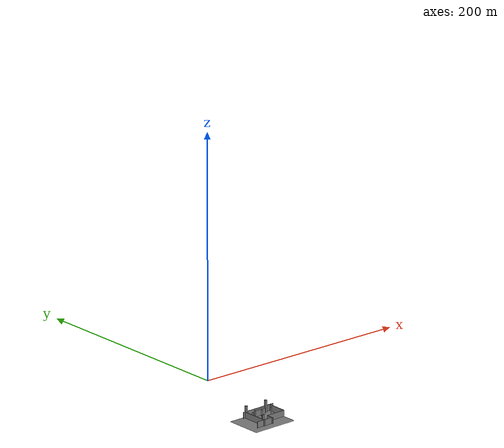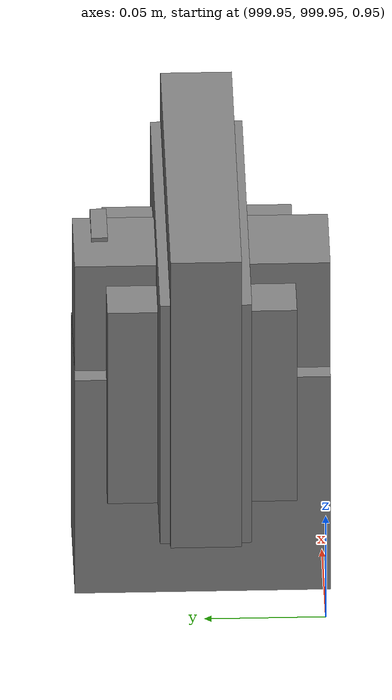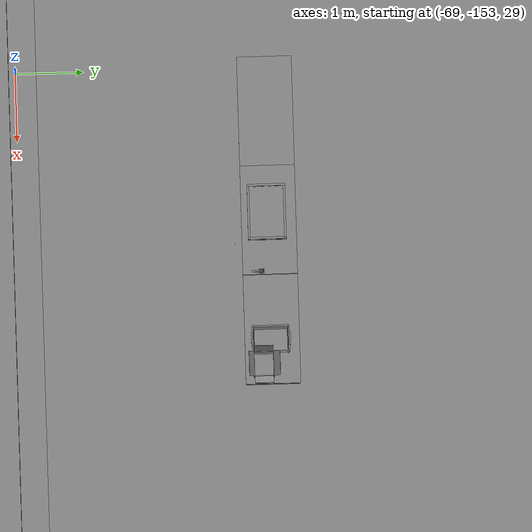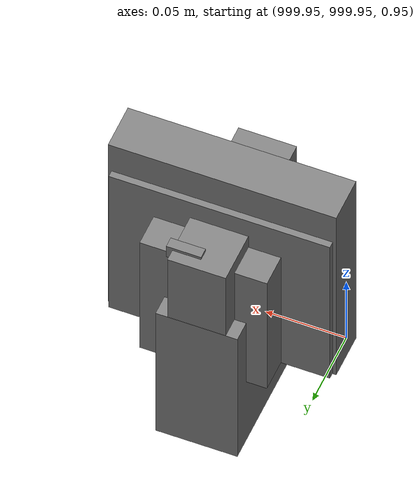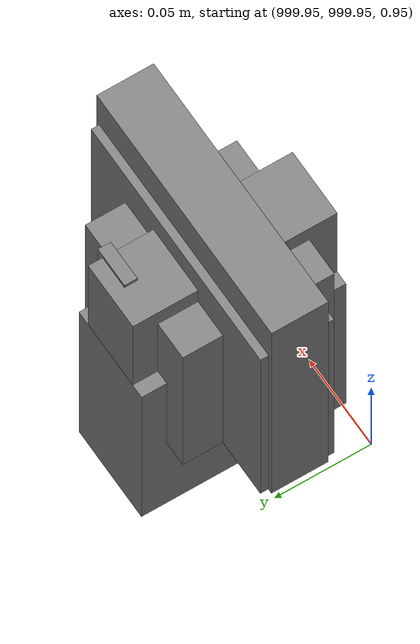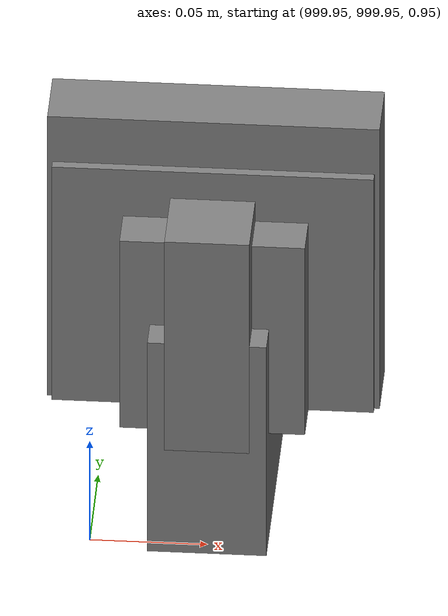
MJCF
<mujoco>
    <option gravity="0.000000000 0.000000000 -9.810000420" timestep="0.0049999999" integrator="implicitfast" density="1.225" viscosity="1.8000001e-05" noslip_iterations="10" iterations="100" sdf_iterations="50">
        <flag multiccd="disable"/>
    </option>
    <size memory="1000M"/>
    <compiler coordinate="local"/>
    <worldbody>
        <light cutoff="30" pos="0 1 1" dir="0 -1 -2"/>
        <light cutoff="30" pos="0 -1 1" dir="0 1 -2"/>
        <body pos="-66.139495850 -149.055068970 31.171577454" euler="-53.991466522 -32.777603149 -103.233619690" mocap="true" name="spotlight1_SpotLight"/>
        <body pos="1000.000000000 999.999938965 1.000000000" euler="0.000000000 0.000000000 180.000000000" name="openloong_gripper_2f85_fix_base_usda_intelcore_i5">
            <geom contype="1" conaffinity="1" density="1000" type="box" material="" rgba="0.500000000 0.500000000 0.500000000 1.000000000" solimp="0.899999976 0.949999988 0.001000000" friction="1.000000000 0.005000000 0.000100000" solref="0.020000000 1.000000000" margin="0" condim="3" group="0" pos="0.000000000 0.000000000 0.051722717" quat="0.707106709 0.000000000 0.000000000 -0.707106769" size="0.052800000 0.018080002 0.052800000" name="openloong_gripper_2f85_fix_base_usda_geom_19010349_6F38_40CE_BBC8_87D0FECB0DBF"/>
            <freejoint name="openloong_gripper_2f85_fix_base_usda_intelcore_i5_joint"/>
            <site size="0.005000000 0.005000000 0.005000000" rgba="0.500000000 0.500000000 0.500000000 1.000000000" pos="0.000000000 0.000000000 0.000000000" quat="0.999961913 0.008726534 0.000000000 0.000000000" group="0" type="sphere" name="openloong_gripper_2f85_fix_base_usda_intelcore_i5site"/>
        </body>
        <body pos="1000.000000000 1000.000000000 1.000000000" euler="0.000011953 0.000005123 -179.999984741" name="openloong_gripper_2f85_fix_base_usda_intel_box">
            <geom contype="1" conaffinity="1" density="1000" type="box" material="" rgba="0.500000000 0.500000000 0.500000000 1.000000000" solimp="0.899999976 0.949999988 0.001000000" friction="1.000000000 0.005000000 0.000100000" solref="0.020000000 1.000000000" margin="0" condim="3" group="0" pos="0.000000000 -0.000067139 0.000082284" quat="0.707106709 0.000000225 0.000000253 0.707106650" size="0.052800003 0.025300000 0.052800003" name="openloong_gripper_2f85_fix_base_usda_geom_1F3C8970_4EFB_4E40_97A5_1DBF199B73EF"/>
            <freejoint name="openloong_gripper_2f85_fix_base_usda_intel_box_joint"/>
            <site size="0.005000000 0.005000000 0.005000000" rgba="0.500000000 0.500000000 0.500000000 1.000000000" pos="0.000000000 0.000000000 0.000000000" quat="0.999961913 0.008726500 0.000000000 0.000000000" group="0" type="sphere" name="openloong_gripper_2f85_fix_base_usda_intel_boxsite"/>
        </body>
        <body pos="1000.000000000 1000.000000000 1.000000000" euler="0.000000000 0.000000000 180.000000000" name="openloong_gripper_2f85_fix_base_usda_wifi_box">
            <geom contype="1" conaffinity="1" density="1000" type="box" material="" rgba="0.500000000 0.500000000 0.500000000 1.000000000" solimp="0.899999976 0.949999988 0.001000000" friction="1.000000000 0.005000000 0.000100000" solref="0.020000000 1.000000000" margin="0" condim="3" group="0" pos="0.000000000 0.000000000 0.058978677" quat="0.000000000 0.000000047 0.000000000 1.000000000" size="0.068499997 0.018999999 0.059000000" name="openloong_gripper_2f85_fix_base_usda_geom_4BB7EB09_5C77_4485_8945_7EB381CB971E"/>
            <freejoint name="openloong_gripper_2f85_fix_base_usda_wifi_box_joint"/>
            <site size="0.005000000 0.005000000 0.005000000" rgba="0.500000000 0.500000000 0.500000000 1.000000000" pos="0.000000000 0.000000000 0.000000000" quat="0.999961913 0.008726500 0.000000000 0.000000000" group="0" type="sphere" name="openloong_gripper_2f85_fix_base_usda_wifi_boxsite"/>
        </body>
        <body pos="1000.000000000 1000.000000000 1.000000000" euler="0.000000000 0.000000000 180.000000000" name="openloong_gripper_2f85_fix_base_usda_cpu_fan">
            <geom contype="1" conaffinity="1" density="1000" type="box" material="" rgba="0.500000000 0.500000000 0.500000000 1.000000000" solimp="0.899999976 0.949999988 0.001000000" friction="1.000000000 0.005000000 0.000100000" solref="0.020000000 1.000000000" margin="0" condim="3" group="0" pos="0.000000000 0.000000000 0.070034981" quat="0.000000000 0.000000000 0.000000000 1.000000000" size="0.070700005 0.014699999 0.070700005" name="openloong_gripper_2f85_fix_base_usda_geom_8DE0A207_7C54_402A_B7FD_3BEE09DCE6BA"/>
            <freejoint name="openloong_gripper_2f85_fix_base_usda_cpu_fan_joint"/>
            <site size="0.005000000 0.005000000 0.005000000" rgba="0.500000000 0.500000000 0.500000000 1.000000000" pos="0.000000000 0.000000000 0.000000000" quat="0.999961913 0.008726535 0.000000000 0.000000000" group="0" type="sphere" name="openloong_gripper_2f85_fix_base_usda_cpu_fancsite"/>
        </body>
        <body pos="-65.963653564 -149.771240234 31.162742615" euler="125.117050171 -86.903648376 -140.641677856" mocap="true" name="spotlight3_SpotLight"/>
        <body pos="1000.000000000 1000.000000000 1.000000000" euler="0.000000000 0.000000000 180.000000000" name="openloong_gripper_2f85_fix_base_usda_battery_01">
            <geom contype="1" conaffinity="1" density="1000" type="box" material="" rgba="0.500000000 0.500000000 0.500000000 1.000000000" solimp="0.899999976 0.949999988 0.001000000" friction="1.000000000 0.005000000 0.000100000" solref="0.020000000 1.000000000" margin="0" condim="3" group="0" pos="-0.011123657 -0.041940309 0.101691343" quat="1.000000000 0.000000000 0.000000000 0.000000000" size="0.010800000 0.003375000 0.004725000" name="openloong_gripper_2f85_fix_base_usda_geom_5A23248B_F301_4581_B92D_8BF8BDD89810"/>
            <geom contype="1" conaffinity="1" density="1000" type="box" material="" rgba="0.500000000 0.500000000 0.500000000 1.000000000" solimp="0.899999976 0.949999988 0.001000000" friction="1.000000000 0.005000000 0.000100000" solref="0.020000000 1.000000000" margin="0" condim="3" group="0" pos="-0.010876465 -0.044247437 0.047066893" quat="0.998702705 -0.050920475 0.000000000 0.000000000" size="0.009450001 0.002700000 0.024975000" name="openloong_gripper_2f85_fix_base_usda_geom_127ED981_C37E_4381_9F71_87EEB4776D99"/>
            <geom contype="1" conaffinity="1" density="1000" type="box" material="" rgba="0.500000000 0.500000000 0.500000000 1.000000000" solimp="0.899999976 0.949999988 0.001000000" friction="1.000000000 0.005000000 0.000100000" solref="0.020000000 1.000000000" margin="0" condim="3" group="0" pos="-0.001235962 -0.000659180 0.047381196" quat="1.000000000 0.000000000 0.000000000 0.000000000" size="0.039420001 0.039150000 0.047250003" name="openloong_gripper_2f85_fix_base_usda_geom_D9B4C62E_9508_4E4B_AC9E_2BD5C17BBE55"/>
            <geom contype="1" conaffinity="1" density="1000" type="box" material="" rgba="0.500000000 0.500000000 0.500000000 1.000000000" solimp="0.899999976 0.949999988 0.001000000" friction="1.000000000 0.005000000 0.000100000" solref="0.020000000 1.000000000" margin="0" condim="3" group="0" pos="-0.010876465 -0.039138794 0.009851727" quat="1.000000000 0.000000000 0.000000000 0.000000000" size="0.009450001 0.010800000 0.013500000" name="openloong_gripper_2f85_fix_base_usda_geom_4F5F0164_5C74_4965_AF8D_82CCDCDF53EF"/>
            <geom contype="1" conaffinity="1" density="1000" type="box" material="" rgba="0.500000000 0.500000000 0.500000000 1.000000000" solimp="0.899999976 0.949999988 0.001000000" friction="1.000000000 0.005000000 0.000100000" solref="0.020000000 1.000000000" margin="0" condim="3" group="0" pos="-0.010876465 -0.041528322 0.071508206" quat="1.000000000 0.000000000 0.000000000 0.000000000" size="0.009450001 0.002700000 0.027000001" name="openloong_gripper_2f85_fix_base_usda_geom_DB2AA9DF_A8C6_49BF_BD0D_DE5908B797E4"/>
            <freejoint name="openloong_gripper_2f85_fix_base_usda_battery_01_joint"/>
            <site size="0.005000000 0.005000000 0.005000000" rgba="0.500000000 0.500000000 0.500000000 1.000000000" pos="0.000000000 0.000000000 0.000000000" quat="0.999961913 0.008726500 0.000000000 0.000000000" group="0" type="sphere" name="openloong_gripper_2f85_fix_base_usda_battery_01site"/>
        </body>
        <body pos="-66.124832153 -149.289794922 31.169359207" euler="-95.441955566 13.992300987 53.340232849" mocap="true" name="spotlight4_SpotLight"/>
        <body pos="-64.866622925 -149.383972168 30.183746338" euler="89.999984741 89.999946594 0.000000000" name="openloong_gripper_2f85_fix_base_usda_bluebox_01">
            <geom contype="1" conaffinity="1" density="1000" type="box" material="" rgba="0.500000000 0.500000000 0.500000000 1.000000000" solimp="0.899999976 0.949999988 0.001000000" friction="1.000000000 0.005000000 0.000100000" solref="0.020000000 1.000000000" margin="0" condim="3" group="0" pos="0.276580811 0.187225342 0.000068665" quat="0.707106948 0.000077471 0.707106352 0.000077486" size="0.100000001 0.057999998 0.010000000" name="openloong_gripper_2f85_fix_base_usda_geom_2A3DB3F7_882F_42F5_8F74_325C5FB7FC19"/>
            <geom contype="1" conaffinity="1" density="1000" type="box" material="" rgba="0.500000000 0.500000000 0.500000000 1.000000000" solimp="0.899999976 0.949999988 0.001000000" friction="1.000000000 0.005000000 0.000100000" solref="0.020000000 1.000000000" margin="0" condim="3" group="0" pos="0.000000000 0.002883911 0.000000000" quat="0.999999881 0.000000000 0.000000000 0.000000000" size="0.254000008 0.003000000 0.172000006" name="openloong_gripper_2f85_fix_base_usda_geom_563CEDCC_D81D_46CC_B28B_BBF9B21E88DA"/>
            <geom contype="1" conaffinity="1" density="1000" type="box" material="" rgba="0.500000000 0.500000000 0.500000000 1.000000000" solimp="0.899999976 0.949999988 0.001000000" friction="1.000000000 0.005000000 0.000100000" solref="0.020000000 1.000000000" margin="0" condim="3" group="0" pos="0.000000000 0.124874115 0.173484802" quat="0.999796331 0.020176515 -0.000000015 0.000000030" size="0.259999990 0.119999997 0.007000000" name="openloong_gripper_2f85_fix_base_usda_geom_156E2633_20D1_4158_9CCA_1014EDBA4588"/>
            <geom contype="1" conaffinity="1" density="1000" type="box" material="" rgba="0.500000000 0.500000000 0.500000000 1.000000000" solimp="0.899999976 0.949999988 0.001000000" friction="1.000000000 0.005000000 0.000100000" solref="0.020000000 1.000000000" margin="0" condim="3" group="0" pos="0.000000000 0.124874115 -0.173469543" quat="0.999796331 -0.020176545 -0.000000015 0.000000000" size="0.259999990 0.119999997 0.007000000" name="openloong_gripper_2f85_fix_base_usda_geom_84206D41_9E58_4BBE_9F85_E55A10701179"/>
            <geom contype="1" conaffinity="1" density="1000" type="box" material="" rgba="0.500000000 0.500000000 0.500000000 1.000000000" solimp="0.899999976 0.949999988 0.001000000" friction="1.000000000 0.005000000 0.000100000" solref="0.020000000 1.000000000" margin="0" condim="3" group="0" pos="0.000000000 0.214008331 0.188980103" quat="0.999912977 0.013176724 0.000000015 0.000000000" size="0.259999990 0.029999999 0.012500000" name="openloong_gripper_2f85_fix_base_usda_geom_6716E45E_011C_4D9D_B405_C1C6BD7F1AE7"/>
            <geom contype="1" conaffinity="1" density="1000" type="box" material="" rgba="0.500000000 0.500000000 0.500000000 1.000000000" solimp="0.899999976 0.949999988 0.001000000" friction="1.000000000 0.005000000 0.000100000" solref="0.020000000 1.000000000" margin="0" condim="3" group="0" pos="-0.258361816 0.125289917 0.001876831" quat="0.702796936 -0.020792112 0.710783124 0.020769298" size="0.189999998 0.119999997 0.009000000" name="openloong_gripper_2f85_fix_base_usda_geom_A1E8C8F2_BC09_443E_8059_466E69294EA9"/>
            <geom contype="1" conaffinity="1" density="1000" type="box" material="" rgba="0.500000000 0.500000000 0.500000000 1.000000000" solimp="0.899999976 0.949999988 0.001000000" friction="1.000000000 0.005000000 0.000100000" solref="0.020000000 1.000000000" margin="0" condim="3" group="0" pos="0.000000000 0.214008331 -0.188980103" quat="0.999912977 -0.013176769 0.000000030 0.000000015" size="0.259999990 0.029999999 0.012500000" name="openloong_gripper_2f85_fix_base_usda_geom_7222DCD9_259C_45A6_A824_B4E8FAF68BDD"/>
            <geom contype="1" conaffinity="1" density="1000" type="box" material="" rgba="0.500000000 0.500000000 0.500000000 1.000000000" solimp="0.899999976 0.949999988 0.001000000" friction="1.000000000 0.005000000 0.000100000" solref="0.020000000 1.000000000" margin="0" condim="3" group="0" pos="-0.276611328 0.187225342 0.000068665" quat="0.707106650 0.000077441 0.707106709 0.000077456" size="0.100000001 0.057999998 0.010000000" name="openloong_gripper_2f85_fix_base_usda_geom_7EF6C43B_0DF6_4F4C_8841_44666AD85A22"/>
            <geom contype="1" conaffinity="1" density="1000" type="box" material="" rgba="0.500000000 0.500000000 0.500000000 1.000000000" solimp="0.899999976 0.949999988 0.001000000" friction="1.000000000 0.005000000 0.000100000" solref="0.020000000 1.000000000" margin="0" condim="3" group="0" pos="0.258331299 0.125289917 0.001876831" quat="0.702851415 0.018856421 0.710823774 -0.019329369" size="0.189999998 0.119999997 0.009000000" name="openloong_gripper_2f85_fix_base_usda_geom_DB788851_B7B4_4526_9C0E_B1B02243329E"/>
            <freejoint name="openloong_gripper_2f85_fix_base_usda_bluebox_01_joint"/>
            <site size="0.005000000 0.005000000 0.005000000" rgba="0.500000000 0.500000000 0.500000000 1.000000000" pos="0.000000000 0.000000000 0.000000000" quat="0.999961913 0.008726534 0.000000000 0.000000000" group="0" type="sphere" name="openloong_gripper_2f85_fix_base_usda_bluebox_01site"/>
        </body>
        <body pos="-64.496299744 -149.491867065 30.235729218" euler="0.000000000 0.000000000 89.999946594" name="openloong_gripper_2f85_fix_base_usda_cardboardbox_01">
            <geom contype="1" conaffinity="1" density="1000" type="box" material="" rgba="0.500000000 0.500000000 0.500000000 1.000000000" solimp="0.899999976 0.949999988 0.001000000" friction="1.000000000 0.005000000 0.000100000" solref="0.020000000 1.000000000" margin="0" condim="3" group="0" pos="-0.003166199 -0.004086494 0.005052090" quat="1.000000000 0.000000000 0.000000000 0.000000000" size="0.142499998 0.177500010 0.005000000" name="openloong_gripper_2f85_fix_base_usda_geom_571DD743_84F3_477E_8E7C_A486F6CB787A"/>
            <geom contype="1" conaffinity="1" density="1000" type="box" material="" rgba="0.500000000 0.500000000 0.500000000 1.000000000" solimp="0.899999976 0.949999988 0.001000000" friction="1.000000000 0.005000000 0.000100000" solref="0.020000000 1.000000000" margin="0" condim="3" group="0" pos="-0.003166199 0.170316696 0.150570869" quat="1.000000000 0.000000000 0.000000000 0.000000000" size="0.142499998 0.005000000 0.149999991" name="openloong_gripper_2f85_fix_base_usda_geom_AC210248_7DBA_4DB7_BC2B_1CE04EC39001"/>
            <geom contype="1" conaffinity="1" density="1000" type="box" material="" rgba="0.500000000 0.500000000 0.500000000 1.000000000" solimp="0.899999976 0.949999988 0.001000000" friction="1.000000000 0.005000000 0.000100000" solref="0.020000000 1.000000000" margin="0" condim="3" group="0" pos="-0.147399902 -0.005307198 0.150570869" quat="1.000000000 0.000000000 0.000000000 0.000000000" size="0.005000000 0.177500010 0.149999991" name="openloong_gripper_2f85_fix_base_usda_geom_0F46213E_A1D7_4E41_B041_A559F56B4179"/>
            <geom contype="1" conaffinity="1" density="1000" type="box" material="" rgba="0.500000000 0.500000000 0.500000000 1.000000000" solimp="0.899999976 0.949999988 0.001000000" friction="1.000000000 0.005000000 0.000100000" solref="0.020000000 1.000000000" margin="0" condim="3" group="0" pos="0.140275955 -0.005307198 0.150570869" quat="1.000000000 0.000000000 0.000000000 0.000000000" size="0.005000000 0.177500010 0.149999991" name="openloong_gripper_2f85_fix_base_usda_geom_9E941E62_92FE_4819_9BFD_96AB79800448"/>
            <geom contype="1" conaffinity="1" density="1000" type="box" material="" rgba="0.500000000 0.500000000 0.500000000 1.000000000" solimp="0.899999976 0.949999988 0.001000000" friction="1.000000000 0.005000000 0.000100000" solref="0.020000000 1.000000000" margin="0" condim="3" group="0" pos="-0.003166199 -0.181550980 0.150570869" quat="1.000000000 0.000000000 0.000000000 0.000000000" size="0.142499998 0.005000000 0.149999991" name="openloong_gripper_2f85_fix_base_usda_geom_51D6BAFC_65A4_4068_B5B3_42600729391E"/>
            <freejoint name="openloong_gripper_2f85_fix_base_usda_cardboardbox_01_joint"/>
            <site size="0.005000000 0.005000000 0.005000000" rgba="0.500000000 0.500000000 0.500000000 1.000000000" pos="0.000000000 0.000000000 0.000000000" quat="0.999961913 0.008726535 0.000000000 0.000000000" group="0" type="sphere" name="openloong_gripper_2f85_fix_base_usda_site_9D0E997C_1EC5_4B72_92A7_30A4AA8887A8"/>
            <body pos="0.139160156 -0.004048347 0.301930904" euler="-179.999954224 49.383502960 179.999954224" name="openloong_gripper_2f85_fix_base_usda_A1_006">
                <geom contype="1" conaffinity="1" density="1000" type="box" material="" rgba="0.500000000 0.500000000 0.500000000 1.000000000" solimp="0.899999976 0.949999988 0.001000000" friction="1.000000000 0.005000000 0.000100000" solref="0.020000000 1.000000000" margin="0" condim="3" group="0" pos="-0.071587563 0.000009537 0.001745224" quat="0.999999881 0.000000000 0.000000000 0.000000000" size="0.071249999 0.179999992 0.002500000" name="openloong_gripper_2f85_fix_base_usda_geom_AB8A8316_9679_4A7E_85CA_495462CBFA04"/>
                <joint armature="0" stiffness="0.07" damping="0.0099999998" axis="0.000000 1.000000 0.000000" type="hinge" name="openloong_gripper_2f85_fix_base_usda_A1_006"/>
            </body>
            <body pos="-0.145902634 -0.004086494 0.301938057" euler="-180.000000000 -60.000011444 -180.000000000" name="openloong_gripper_2f85_fix_base_usda_A2_006">
                <geom contype="1" conaffinity="1" density="1000" type="box" material="" rgba="0.500000000 0.500000000 0.500000000 1.000000000" solimp="0.899999976 0.949999988 0.001000000" friction="1.000000000 0.005000000 0.000100000" solref="0.020000000 1.000000000" margin="0" condim="3" group="0" pos="0.071268082 0.000009537 0.002717972" quat="0.000002921 0.000000000 -0.000000030 0.999999881" size="0.071249999 0.179999992 0.002500000" name="openloong_gripper_2f85_fix_base_usda_geom_3551B0B1_8303_40E3_9DB0_03ECACA2B016"/>
                <joint armature="0" stiffness="0.07" damping="0.0099999998" axis="0.000000 1.000000 0.000000" type="hinge" name="openloong_gripper_2f85_fix_base_usda_A2_006"/>
            </body>
            <body pos="-0.003385544 0.175991058 0.301930904" euler="-125.858116150 -0.000004561 0.000002331" name="openloong_gripper_2f85_fix_base_usda_B2_006">
                <geom contype="1" conaffinity="1" density="1000" type="box" material="" rgba="0.500000000 0.500000000 0.500000000 1.000000000" solimp="0.899999976 0.949999988 0.001000000" friction="1.000000000 0.005000000 0.000100000" solref="0.020000000 1.000000000" margin="0" condim="3" group="0" pos="0.000009537 -0.070939064 -0.002470016" quat="0.999614120 0.027776197 -0.000000015 0.000000030" size="0.137500003 0.064999998 0.005000000" name="openloong_gripper_2f85_fix_base_usda_geom_E94D1B22_5522_4D75_970B_2F63D5736E12"/>
                <joint armature="0" stiffness="0.07" damping="0.0099999998" axis="1.000000 0.000000 0.000000" type="hinge" name="openloong_gripper_2f85_fix_base_usda_B2_006"/>
            </body>
            <body pos="-0.003385544 -0.184140205 0.301938057" euler="147.805557251 0.000000000 0.000000000" name="openloong_gripper_2f85_fix_base_usda_B1_006">
                <geom contype="1" conaffinity="1" density="1000" type="box" material="" rgba="0.500000000 0.500000000 0.500000000 1.000000000" solimp="0.899999976 0.949999988 0.001000000" friction="1.000000000 0.005000000 0.000100000" solref="0.020000000 1.000000000" margin="0" condim="3" group="0" pos="-0.000028610 0.070202351 -0.002703667" quat="0.999614179 -0.027776167 0.000000000 0.000000000" size="0.137500003 0.064999998 0.005000000" name="openloong_gripper_2f85_fix_base_usda_geom_8EF489FF_1A94_40CF_AB7C_FF907DAF85D3"/>
                <joint armature="0" stiffness="0.07" damping="0.0099999998" axis="1.000000 0.000000 0.000000" type="hinge" name="openloong_gripper_2f85_fix_base_usda_B1_006"/>
            </body>
        </body>
        <body pos="-65.882858276 -149.481979370 30.229999542" euler="-64.487716675 0.000000000 0.000000000" name="openloong_gripper_2f85_fix_base_usda_Barcode">
            <geom contype="1" conaffinity="1" density="1000" type="box" material="" rgba="0.500000000 0.500000000 0.500000000 1.000000000" solimp="0.899999976 0.949999988 0.001000000" friction="1.000000000 0.005000000 0.000100000" solref="0.020000000 1.000000000" margin="0" condim="3" group="0" pos="0.000000000 0.013038635 0.001419067" quat="0.000000000 0.000000000 0.000000000 1.000000119" size="0.034000002 0.010000000 0.017999999" name="openloong_gripper_2f85_fix_base_usda_geom_0786D058_B032_46F5_9788_950B4E701754"/>
            <geom contype="1" conaffinity="1" density="1000" type="box" material="" rgba="0.500000000 0.500000000 0.500000000 1.000000000" solimp="0.899999976 0.949999988 0.001000000" friction="1.000000000 0.005000000 0.000100000" solref="0.020000000 1.000000000" margin="0" condim="3" group="0" pos="0.000000000 -0.035301208 -0.007095337" quat="0.000000000 0.000000000 -0.043619365 0.999048233" size="0.028999999 0.010000000 0.020000000" name="openloong_gripper_2f85_fix_base_usda_geom_ADDC28E3_18A7_4E05_919C_885A90F2EDA1"/>
            <geom contype="1" conaffinity="1" density="1000" type="box" material="" rgba="0.500000000 0.500000000 0.500000000 1.000000000" solimp="0.899999976 0.949999988 0.001000000" friction="1.000000000 0.005000000 0.000100000" solref="0.020000000 1.000000000" margin="0" condim="3" group="0" pos="0.000000000 -0.043411255 -0.011749268" quat="0.922262907 0.386563420 0.000000000 0.000000000" size="0.026000001 0.010000000 0.020000000" name="openloong_gripper_2f85_fix_base_usda_geom_6DAC00CE_EEBF_4FE5_AD65_5CF5A38AEF62"/>
            <geom contype="1" conaffinity="1" density="1000" type="box" material="" rgba="0.500000000 0.500000000 0.500000000 1.000000000" solimp="0.899999976 0.949999988 0.001000000" friction="1.000000000 0.005000000 0.000100000" solref="0.020000000 1.000000000" margin="0" condim="3" group="0" pos="0.000000000 -0.016967773 -0.031860352" quat="0.000000000 0.000000000 0.000000000 1.000000119" size="0.008000000 0.010000000 0.013000000" name="openloong_gripper_2f85_fix_base_usda_geom_D8FB78AB_007B_4D34_91B9_79AAD4350722"/>
            <geom contype="1" conaffinity="1" density="1000" type="box" material="" rgba="0.500000000 0.500000000 0.500000000 1.000000000" solimp="0.899999976 0.949999988 0.001000000" friction="1.000000000 0.005000000 0.000100000" solref="0.020000000 1.000000000" margin="0" condim="3" group="0" pos="0.000000000 -0.001869202 0.000312805" quat="0.953716993 0.300705761 0.000000000 0.000000000" size="0.032000002 0.010000000 0.018999999" name="openloong_gripper_2f85_fix_base_usda_geom_0C51DDAB_7AB8_40EA_AB35_AF01E648832A"/>
            <geom contype="1" conaffinity="1" density="1000" type="box" material="" rgba="0.500000000 0.500000000 0.500000000 1.000000000" solimp="0.899999976 0.949999988 0.001000000" friction="1.000000000 0.005000000 0.000100000" solref="0.020000000 1.000000000" margin="0" condim="3" group="0" pos="0.000000000 -0.019531250 -0.003173828" quat="0.953716993 0.300705761 0.000000000 0.000000000" size="0.030999999 0.010000000 0.020000000" name="openloong_gripper_2f85_fix_base_usda_geom_2AB39273_7FF1_4696_9FB8_A723CBE2EE47"/>
            <geom contype="1" conaffinity="1" density="1000" type="box" material="" rgba="0.500000000 0.500000000 0.500000000 1.000000000" solimp="0.899999976 0.949999988 0.001000000" friction="1.000000000 0.005000000 0.000100000" solref="0.020000000 1.000000000" margin="0" condim="3" group="0" pos="0.000000000 -0.035301208 -0.007095337" quat="0.953716993 0.300705761 0.000000000 0.000000000" size="0.028999999 0.010000000 0.020000000" name="openloong_gripper_2f85_fix_base_usda_geom_DC90183C_8C43_4F78_911E_8F6815C40585"/>
            <geom contype="1" conaffinity="1" density="1000" type="box" material="" rgba="0.500000000 0.500000000 0.500000000 1.000000000" solimp="0.899999976 0.949999988 0.001000000" friction="1.000000000 0.005000000 0.000100000" solref="0.020000000 1.000000000" margin="0" condim="3" group="0" pos="0.000000000 -0.042617798 -0.071121216" quat="0.000000000 0.000000000 0.000000000 1.000000119" size="0.013000000 0.021000000 0.059999999" name="openloong_gripper_2f85_fix_base_usda_geom_49B39BA0_FBDF_4B3A_9103_221FD2986E7F"/>
            <freejoint name="openloong_gripper_2f85_fix_base_usda_Barcode_joint"/>
            <site size="0.005000000 0.005000000 0.005000000" rgba="0.500000000 0.500000000 0.500000000 1.000000000" pos="0.000000000 0.000000000 0.000000000" quat="1.000000000 0.000000000 0.000000000 0.000000000" group="0" type="sphere" name="openloong_gripper_2f85_fix_base_usda_Barcode_site"/>
        </body>
        <body pos="-66.745018005 -149.392349243 30.184000015" euler="0.000000000 0.000000000 89.999946594" name="[22332958882346]_Basket_01">
            <geom contype="1" conaffinity="1" density="1000" type="box" material="" rgba="0.500000000 0.500000000 0.500000000 1.000000000" solimp="0.899999976 0.949999988 0.001000000" friction="1.000000000 0.005000000 0.000100000" solref="0.020000000 1.000000000" margin="0" condim="3" group="0" pos="-0.052425385 0.389207840 0.089787483" quat="0.707107008 0.000000000 0.000000000 0.707106411" size="0.014249999 0.014249999 0.059999999" name="[22332958882346]_geom_616B56F8_6239_46FA_A718_48EF0B6EEAA8"/>
            <geom contype="1" conaffinity="1" density="1000" type="box" material="" rgba="0.500000000 0.500000000 0.500000000 1.000000000" solimp="0.899999976 0.949999988 0.001000000" friction="1.000000000 0.005000000 0.000100000" solref="0.020000000 1.000000000" margin="0" condim="3" group="0" pos="0.264015198 -0.133043289 0.089787483" quat="0.707107008 0.000000000 0.000000000 0.707106411" size="0.014249999 0.014249999 0.059999999" name="[22332958882346]_geom_B76C650C_0B22_4B8B_963B_A8045412C245"/>
            <geom contype="1" conaffinity="1" density="1000" type="box" material="" rgba="0.500000000 0.500000000 0.500000000 1.000000000" solimp="0.899999976 0.949999988 0.001000000" friction="1.000000000 0.005000000 0.000100000" solref="0.020000000 1.000000000" margin="0" condim="3" group="0" pos="-0.264015198 -0.265548706 0.089793205" quat="0.707107008 0.000000000 0.000000000 0.707106411" size="0.014249999 0.014249999 0.059999999" name="[22332958882346]_geom_17092B23_12DF_4229_8136_3D610138484A"/>
            <geom contype="1" conaffinity="1" density="1000" type="box" material="" rgba="0.500000000 0.500000000 0.500000000 1.000000000" solimp="0.899999976 0.949999988 0.001000000" friction="1.000000000 0.005000000 0.000100000" solref="0.020000000 1.000000000" margin="0" condim="3" group="0" pos="-0.160263062 -0.389322281 0.089793205" quat="0.707107008 0.000000000 0.000000000 0.707106411" size="0.014249999 0.014249999 0.059999999" name="[22332958882346]_geom_0DDAF35C_3C99_456C_9B7E_80777D505E24"/>
            <geom contype="1" conaffinity="1" density="1000" type="box" material="" rgba="0.500000000 0.500000000 0.500000000 1.000000000" solimp="0.899999976 0.949999988 0.001000000" friction="1.000000000 0.005000000 0.000100000" solref="0.020000000 1.000000000" margin="0" condim="3" group="0" pos="0.162265778 -0.389322281 0.089787483" quat="0.707107008 0.000000000 0.000000000 0.707106411" size="0.014249999 0.014249999 0.059999999" name="[22332958882346]_geom_9D864287_78FE_4859_924C_704251911A72"/>
            <geom contype="1" conaffinity="1" density="1000" type="box" material="" rgba="0.500000000 0.500000000 0.500000000 1.000000000" solimp="0.899999976 0.949999988 0.001000000" friction="1.000000000 0.005000000 0.000100000" solref="0.020000000 1.000000000" margin="0" condim="3" group="0" pos="0.264015198 0.389207840 0.089787483" quat="0.707107008 0.000000000 0.000000000 0.707106411" size="0.014249999 0.014249999 0.059999999" name="[22332958882346]_geom_37ADF976_9261_42A5_BB86_E021BD427B41"/>
            <geom contype="1" conaffinity="1" density="1000" type="box" material="" rgba="0.500000000 0.500000000 0.500000000 1.000000000" solimp="0.899999976 0.949999988 0.001000000" friction="1.000000000 0.005000000 0.000100000" solref="0.020000000 1.000000000" margin="0" condim="3" group="0" pos="-0.264015198 -0.133043289 0.089793205" quat="0.707107008 0.000000000 0.000000000 0.707106411" size="0.014249999 0.014249999 0.059999999" name="[22332958882346]_geom_AA0C4AB0_E755_43AE_97D3_260D7B1572CF"/>
            <geom contype="1" conaffinity="1" density="1000" type="box" material="" rgba="0.500000000 0.500000000 0.500000000 1.000000000" solimp="0.899999976 0.949999988 0.001000000" friction="1.000000000 0.005000000 0.000100000" solref="0.020000000 1.000000000" margin="0" condim="3" group="0" pos="-0.264026642 0.269256592 0.089793205" quat="0.707107008 0.000000000 0.000000000 0.707106411" size="0.014249999 0.014249999 0.059999999" name="[22332958882346]_geom_AA373364_9E96_4306_89F6_CD078E18B8FA"/>
            <geom contype="1" conaffinity="1" density="1000" type="box" material="" rgba="0.500000000 0.500000000 0.500000000 1.000000000" solimp="0.899999976 0.949999988 0.001000000" friction="1.000000000 0.005000000 0.000100000" solref="0.020000000 1.000000000" margin="0" condim="3" group="0" pos="0.054462433 0.389207840 0.089787483" quat="0.707107008 0.000000000 0.000000000 0.707106411" size="0.014249999 0.014249999 0.059999999" name="[22332958882346]_geom_58E388BD_DDCD_4E9F_836E_7A6137DEBACE"/>
            <geom contype="1" conaffinity="1" density="1000" type="box" material="" rgba="0.500000000 0.500000000 0.500000000 1.000000000" solimp="0.899999976 0.949999988 0.001000000" friction="1.000000000 0.005000000 0.000100000" solref="0.020000000 1.000000000" margin="0" condim="3" group="0" pos="0.054462433 -0.389322281 0.089787483" quat="0.707107008 0.000000000 0.000000000 0.707106411" size="0.014249999 0.014249999 0.059999999" name="[22332958882346]_geom_5EB17239_07C7_491C_9A74_7D3EAAC159A0"/>
            <geom contype="1" conaffinity="1" density="1000" type="box" material="" rgba="0.500000000 0.500000000 0.500000000 1.000000000" solimp="0.899999976 0.949999988 0.001000000" friction="1.000000000 0.005000000 0.000100000" solref="0.020000000 1.000000000" margin="0" condim="3" group="0" pos="0.264015198 0.269256592 0.089793205" quat="0.707107008 0.000000000 0.000000000 0.707106411" size="0.014249999 0.014249999 0.059999999" name="[22332958882346]_geom_99749C92_9678_4928_8AFB_711568C18480"/>
            <geom contype="1" conaffinity="1" density="1000" type="box" material="" rgba="0.500000000 0.500000000 0.500000000 1.000000000" solimp="0.899999976 0.949999988 0.001000000" friction="1.000000000 0.005000000 0.000100000" solref="0.020000000 1.000000000" margin="0" condim="3" group="0" pos="0.264015198 -0.389322281 0.089787483" quat="0.707107008 0.000000000 0.000000000 0.707106411" size="0.014249999 0.014249999 0.059999999" name="[22332958882346]_geom_869A0AA9_A7F6_4956_BF15_B722C1E5DC8C"/>
            <geom contype="1" conaffinity="1" density="1000" type="box" material="" rgba="0.500000000 0.500000000 0.500000000 1.000000000" solimp="0.899999976 0.949999988 0.001000000" friction="1.000000000 0.005000000 0.000100000" solref="0.020000000 1.000000000" margin="0" condim="3" group="0" pos="0.000000000 0.000000000 0.015998840" quat="0.707107008 0.000000000 0.000000000 0.707106411" size="0.403499991 0.279000014 0.015750000" name="[22332958882346]_geom_DCB7006F_F676_4383_92AA_3613D1CA64E0"/>
            <geom contype="1" conaffinity="1" density="1000" type="box" material="" rgba="0.500000000 0.500000000 0.500000000 1.000000000" solimp="0.899999976 0.949999988 0.001000000" friction="1.000000000 0.005000000 0.000100000" solref="0.020000000 1.000000000" margin="0" condim="3" group="0" pos="0.000000000 -0.389476776 0.163619041" quat="0.707107008 0.000000000 0.000000000 0.707106411" size="0.015000000 0.277500004 0.015750000" name="[22332958882346]_geom_E0B80BF6_094B_4DA1_8563_BD29EDF9DAD5"/>
            <geom contype="1" conaffinity="1" density="1000" type="box" material="" rgba="0.500000000 0.500000000 0.500000000 1.000000000" solimp="0.899999976 0.949999988 0.001000000" friction="1.000000000 0.005000000 0.000100000" solref="0.020000000 1.000000000" margin="0" condim="3" group="0" pos="0.162265778 0.389207840 0.089787483" quat="0.707107008 0.000000000 0.000000000 0.707106411" size="0.014249999 0.014249999 0.059999999" name="[22332958882346]_geom_24FCB00D_00B1_4AFD_AC99_D6F59B21D268"/>
            <geom contype="1" conaffinity="1" density="1000" type="box" material="" rgba="0.500000000 0.500000000 0.500000000 1.000000000" solimp="0.899999976 0.949999988 0.001000000" friction="1.000000000 0.005000000 0.000100000" solref="0.020000000 1.000000000" margin="0" condim="3" group="0" pos="0.000000000 0.389471054 0.163619041" quat="0.707107008 0.000000000 0.000000000 0.707106411" size="0.015000000 0.277500004 0.015750000" name="[22332958882346]_geom_9165FBF3_E1B9_4A0B_B7FB_046121593446"/>
            <geom contype="1" conaffinity="1" density="1000" type="box" material="" rgba="0.500000000 0.500000000 0.500000000 1.000000000" solimp="0.899999976 0.949999988 0.001000000" friction="1.000000000 0.005000000 0.000100000" solref="0.020000000 1.000000000" margin="0" condim="3" group="0" pos="-0.263511658 0.000000000 0.163619041" quat="0.707107008 0.000000000 0.000000000 0.707106411" size="0.403499991 0.015000000 0.015750000" name="[22332958882346]_geom_0DBCFE54_1674_4A06_8873_247D6C352C6F"/>
            <geom contype="1" conaffinity="1" density="1000" type="box" material="" rgba="0.500000000 0.500000000 0.500000000 1.000000000" solimp="0.899999976 0.949999988 0.001000000" friction="1.000000000 0.005000000 0.000100000" solref="0.020000000 1.000000000" margin="0" condim="3" group="0" pos="-0.264015198 0.141334534 0.089793205" quat="0.707107008 0.000000000 0.000000000 0.707106411" size="0.014249999 0.014249999 0.059999999" name="[22332958882346]_geom_438294ED_DC16_4432_98B8_69FA99A1F3A0"/>
            <geom contype="1" conaffinity="1" density="1000" type="box" material="" rgba="0.500000000 0.500000000 0.500000000 1.000000000" solimp="0.899999976 0.949999988 0.001000000" friction="1.000000000 0.005000000 0.000100000" solref="0.020000000 1.000000000" margin="0" condim="3" group="0" pos="0.264015198 -0.265548706 0.089787483" quat="0.707107008 0.000000000 0.000000000 0.707106411" size="0.014249999 0.014249999 0.059999999" name="[22332958882346]_geom_C46387E1_13DA_414A_BD7F_E96BC6139A3E"/>
            <geom contype="1" conaffinity="1" density="1000" type="box" material="" rgba="0.500000000 0.500000000 0.500000000 1.000000000" solimp="0.899999976 0.949999988 0.001000000" friction="1.000000000 0.005000000 0.000100000" solref="0.020000000 1.000000000" margin="0" condim="3" group="0" pos="-0.160263062 0.389207840 0.089787483" quat="0.707107008 0.000000000 0.000000000 0.707106411" size="0.014249999 0.014249999 0.059999999" name="[22332958882346]_geom_992E134F_61BC_4FA5_A6FF_54876FEF83A1"/>
            <geom contype="1" conaffinity="1" density="1000" type="box" material="" rgba="0.500000000 0.500000000 0.500000000 1.000000000" solimp="0.899999976 0.949999988 0.001000000" friction="1.000000000 0.005000000 0.000100000" solref="0.020000000 1.000000000" margin="0" condim="3" group="0" pos="-0.052425385 -0.389322281 0.089787483" quat="0.707107008 0.000000000 0.000000000 0.707106411" size="0.014249999 0.014249999 0.059999999" name="[22332958882346]_geom_F1569F30_6A1A_454E_A8EC_83951C59D7C4"/>
            <geom contype="1" conaffinity="1" density="1000" type="box" material="" rgba="0.500000000 0.500000000 0.500000000 1.000000000" solimp="0.899999976 0.949999988 0.001000000" friction="1.000000000 0.005000000 0.000100000" solref="0.020000000 1.000000000" margin="0" condim="3" group="0" pos="-0.264026642 -0.389322281 0.089793205" quat="0.707107008 0.000000000 0.000000000 0.707106411" size="0.014249999 0.014249999 0.059999999" name="[22332958882346]_geom_15AA4275_F7DF_43C5_974B_C6DE78616CBB"/>
            <geom contype="1" conaffinity="1" density="1000" type="box" material="" rgba="0.500000000 0.500000000 0.500000000 1.000000000" solimp="0.899999976 0.949999988 0.001000000" friction="1.000000000 0.005000000 0.000100000" solref="0.020000000 1.000000000" margin="0" condim="3" group="0" pos="0.264015198 0.141334534 0.089787483" quat="0.707107008 0.000000000 0.000000000 0.707106411" size="0.014249999 0.014249999 0.059999999" name="[22332958882346]_geom_6046CFC6_DED4_4C02_BCD7_38907784F52D"/>
            <geom contype="1" conaffinity="1" density="1000" type="box" material="" rgba="0.500000000 0.500000000 0.500000000 1.000000000" solimp="0.899999976 0.949999988 0.001000000" friction="1.000000000 0.005000000 0.000100000" solref="0.020000000 1.000000000" margin="0" condim="3" group="0" pos="-0.264015198 0.389207840 0.089793205" quat="0.707107008 0.000000000 0.000000000 0.707106411" size="0.014249999 0.014249999 0.059999999" name="[22332958882346]_geom_0B7D3DC9_B441_4586_B4E5_24C5C7F477F2"/>
            <geom contype="1" conaffinity="1" density="1000" type="box" material="" rgba="0.500000000 0.500000000 0.500000000 1.000000000" solimp="0.899999976 0.949999988 0.001000000" friction="1.000000000 0.005000000 0.000100000" solref="0.020000000 1.000000000" margin="0" condim="3" group="0" pos="0.264015198 0.004480362 0.089787483" quat="0.707107008 0.000000000 0.000000000 0.707106411" size="0.014249999 0.014249999 0.059999999" name="[22332958882346]_geom_75C8C91D_9FED_42B3_8053_4430C44C08FA"/>
            <geom contype="1" conaffinity="1" density="1000" type="box" material="" rgba="0.500000000 0.500000000 0.500000000 1.000000000" solimp="0.899999976 0.949999988 0.001000000" friction="1.000000000 0.005000000 0.000100000" solref="0.020000000 1.000000000" margin="0" condim="3" group="0" pos="0.263694763 -0.000011444 0.163619041" quat="0.707107008 0.000000000 0.000000000 0.707106411" size="0.403499991 0.015000000 0.015750000" name="[22332958882346]_geom_D797EA2C_5173_4C84_BE95_76FD115D9437"/>
            <geom contype="1" conaffinity="1" density="1000" type="box" material="" rgba="0.500000000 0.500000000 0.500000000 1.000000000" solimp="0.899999976 0.949999988 0.001000000" friction="1.000000000 0.005000000 0.000100000" solref="0.020000000 1.000000000" margin="0" condim="3" group="0" pos="-0.264015198 0.004480362 0.089793205" quat="0.707107008 0.000000000 0.000000000 0.707106411" size="0.014249999 0.014249999 0.059999999" name="[22332958882346]_geom_749CFB49_5C0B_46F5_B3CF_DBC48E0055E4"/>
            <freejoint name="[22332958882346]_joint_7025BB84_AB80_4476_8DC1_A41B016E02F4"/>
        </body>
        <body pos="0.000000000 0.000000000 0.000000000" euler="0.000000000 0.000000000 0.000000000" name="Static Objects_Static Objects">
            <geom contype="1" conaffinity="1" density="1000" type="box" material="" rgba="0.500000000 0.500000000 0.500000000 1.000000000" solimp="0.899999976 0.949999988 0.001000000" friction="1.000000000 0.005000000 0.000100000" solref="0.020000000 1.000000000" margin="0" condim="3" group="0" pos="-67.544113159 -149.365814209 29.727830887" quat="0.500000417 0.499999970 0.499999553 0.499999970" size="0.381000012 0.319999993 0.041000001" name="Static Objects_geom_1465EB32_C2A7_4724_8178_C4EAA5EE415D"/>
            <geom contype="1" conaffinity="1" density="1000" type="box" material="" rgba="0.500000000 0.500000000 0.500000000 1.000000000" solimp="0.899999976 0.949999988 0.001000000" friction="1.000000000 0.005000000 0.000100000" solref="0.020000000 1.000000000" margin="0" condim="3" group="0" pos="-68.239501953 -149.365814209 30.086868286" quat="0.500000417 0.499999970 0.499999553 0.499999970" size="0.370999992 0.039500002 0.745000005" name="Static Objects_geom_7946D996_B24C_45B6_83B2_CEE26DE13DCE"/>
            <geom contype="1" conaffinity="1" density="1000" type="box" material="" rgba="0.500000000 0.500000000 0.500000000 1.000000000" solimp="0.899999976 0.949999988 0.001000000" friction="1.000000000 0.005000000 0.000100000" solref="0.020000000 1.000000000" margin="0" condim="3" group="0" pos="-68.239501953 -149.365814209 30.147235870" quat="0.500000417 0.499999970 0.499999553 0.499999970" size="0.400000006 0.022000000 0.800000012" name="Static Objects_geom_95C02462_78FD_4418_BE27_3CD7146A4F84"/>
            <geom contype="1" conaffinity="1" density="1000" type="box" material="" rgba="0.500000000 0.500000000 0.500000000 1.000000000" solimp="0.899999976 0.949999988 0.001000000" friction="1.000000000 0.005000000 0.000100000" solref="0.020000000 1.000000000" margin="0" condim="3" group="0" pos="-68.934890747 -149.365814209 29.727830887" quat="0.500000417 0.499999970 0.499999553 0.499999970" size="0.381000012 0.319999993 0.041000001" name="Static Objects_geom_6A42D1AC_924D_427C_B93B_BB24CB6E6FDF"/>
            <geom contype="1" conaffinity="1" density="1000" type="box" material="" rgba="0.500000000 0.500000000 0.500000000 1.000000000" solimp="0.899999976 0.949999988 0.001000000" friction="1.000000000 0.005000000 0.000100000" solref="0.020000000 1.000000000" margin="0" condim="3" group="0" pos="-68.239501953 -149.365814209 29.561563492" quat="0.500000417 0.499999970 0.499999553 0.499999970" size="0.020000000 0.022000000 0.660000026" name="Static Objects_geom_388A04F6_B765_4306_92C1_0525B0F19B21"/>
            <geom contype="1" conaffinity="1" density="1000" type="box" material="" rgba="0.500000000 0.500000000 0.500000000 1.000000000" solimp="0.899999976 0.949999988 0.001000000" friction="1.000000000 0.005000000 0.000100000" solref="0.020000000 1.000000000" margin="0" condim="3" group="0" pos="-65.945671082 -149.365814209 29.727830887" quat="0.500000417 0.499999970 0.499999553 0.499999970" size="0.381000012 0.319999993 0.041000001" name="Static Objects_geom_855F156E_B677_4000_A738_9FEB2D1055B6"/>
            <geom contype="1" conaffinity="1" density="1000" type="box" material="" rgba="0.500000000 0.500000000 0.500000000 1.000000000" solimp="0.899999976 0.949999988 0.001000000" friction="1.000000000 0.005000000 0.000100000" solref="0.020000000 1.000000000" margin="0" condim="3" group="0" pos="-66.641059875 -149.365814209 30.086868286" quat="0.500000417 0.499999970 0.499999553 0.499999970" size="0.370999992 0.039500002 0.745000005" name="Static Objects_geom_4D6CED9A_9224_4B4C_B74D_E17D94D7E548"/>
            <geom contype="1" conaffinity="1" density="1000" type="box" material="" rgba="0.500000000 0.500000000 0.500000000 1.000000000" solimp="0.899999976 0.949999988 0.001000000" friction="1.000000000 0.005000000 0.000100000" solref="0.020000000 1.000000000" margin="0" condim="3" group="0" pos="-66.641059875 -149.365814209 30.147235870" quat="0.500000417 0.499999970 0.499999553 0.499999970" size="0.400000006 0.022000000 0.800000012" name="Static Objects_geom_D84E6709_C014_449C_94C4_2FDB507C1101"/>
            <geom contype="1" conaffinity="1" density="1000" type="box" material="" rgba="0.500000000 0.500000000 0.500000000 1.000000000" solimp="0.899999976 0.949999988 0.001000000" friction="1.000000000 0.005000000 0.000100000" solref="0.020000000 1.000000000" margin="0" condim="3" group="0" pos="-67.336448669 -149.365814209 29.727830887" quat="0.500000417 0.499999970 0.499999553 0.499999970" size="0.381000012 0.319999993 0.041000001" name="Static Objects_geom_0EE7B9E8_9E90_4BC3_8BB0_071FB48C6B84"/>
            <geom contype="1" conaffinity="1" density="1000" type="box" material="" rgba="0.500000000 0.500000000 0.500000000 1.000000000" solimp="0.899999976 0.949999988 0.001000000" friction="1.000000000 0.005000000 0.000100000" solref="0.020000000 1.000000000" margin="0" condim="3" group="0" pos="-66.641059875 -149.365814209 29.561563492" quat="0.500000417 0.499999970 0.499999553 0.499999970" size="0.020000000 0.022000000 0.660000026" name="Static Objects_geom_14A69725_8573_4E03_8678_A5B8400D3D39"/>
            <geom contype="1" conaffinity="1" density="1000" type="box" material="" rgba="0.500000000 0.500000000 0.500000000 1.000000000" solimp="0.899999976 0.949999988 0.001000000" friction="1.000000000 0.005000000 0.000100000" solref="0.020000000 1.000000000" margin="0" condim="3" group="0" pos="-64.338577271 -149.365814209 29.727830887" quat="0.500000417 0.499999970 0.499999553 0.499999970" size="0.381000012 0.319999993 0.041000001" name="Static Objects_geom_95690FEB_5D64_452B_A99F_B802C4548E96"/>
            <geom contype="1" conaffinity="1" density="1000" type="box" material="" rgba="0.500000000 0.500000000 0.500000000 1.000000000" solimp="0.899999976 0.949999988 0.001000000" friction="1.000000000 0.005000000 0.000100000" solref="0.020000000 1.000000000" margin="0" condim="3" group="0" pos="-65.033966064 -149.365814209 30.086868286" quat="0.500000417 0.499999970 0.499999553 0.499999970" size="0.370999992 0.039500002 0.745000005" name="Static Objects_geom_12878502_DA54_493D_B9A3_7D7C49BEA005"/>
            <geom contype="1" conaffinity="1" density="1000" type="box" material="" rgba="0.500000000 0.500000000 0.500000000 1.000000000" solimp="0.899999976 0.949999988 0.001000000" friction="1.000000000 0.005000000 0.000100000" solref="0.020000000 1.000000000" margin="0" condim="3" group="0" pos="-65.033966064 -149.365814209 30.147235870" quat="0.500000417 0.499999970 0.499999553 0.499999970" size="0.400000006 0.022000000 0.800000012" name="Static Objects_geom_6F4B2FC6_9A36_4C0A_9B26_85FC6738EDE6"/>
            <geom contype="1" conaffinity="1" density="1000" type="box" material="" rgba="0.500000000 0.500000000 0.500000000 1.000000000" solimp="0.899999976 0.949999988 0.001000000" friction="1.000000000 0.005000000 0.000100000" solref="0.020000000 1.000000000" margin="0" condim="3" group="0" pos="-65.729354858 -149.365814209 29.727830887" quat="0.500000417 0.499999970 0.499999553 0.499999970" size="0.381000012 0.319999993 0.041000001" name="Static Objects_geom_D831F746_10E1_4B81_9F44_7B984FEF20BE"/>
            <geom contype="1" conaffinity="1" density="1000" type="box" material="" rgba="0.500000000 0.500000000 0.500000000 1.000000000" solimp="0.899999976 0.949999988 0.001000000" friction="1.000000000 0.005000000 0.000100000" solref="0.020000000 1.000000000" margin="0" condim="3" group="0" pos="-65.033966064 -149.365814209 29.561563492" quat="0.500000417 0.499999970 0.499999553 0.499999970" size="0.020000000 0.022000000 0.660000026" name="Static Objects_geom_5C655F34_9198_4773_BBD0_34161F2E8D47"/>
            <geom contype="1" conaffinity="1" density="1000" type="box" material="" rgba="0.500000000 0.500000000 0.500000000 1.000000000" solimp="0.899999976 0.949999988 0.001000000" friction="1.000000000 0.005000000 0.000100000" solref="0.020000000 1.000000000" margin="0" condim="3" group="0" pos="-61.754566193 -137.853729248 33.906845093" quat="0.707107067 0.000000000 0.000000000 0.707106471" size="0.759999990 0.759999990 4.500000000" name="Static Objects_geom_2B76BD30_636E_42E0_97BF_681D3D035AC8"/>
            <geom contype="1" conaffinity="1" density="1000" type="box" material="" rgba="0.500000000 0.500000000 0.500000000 1.000000000" solimp="0.899999976 0.949999988 0.001000000" friction="1.000000000 0.005000000 0.000100000" solref="0.020000000 1.000000000" margin="0" condim="3" group="0" pos="-57.511135101 -144.927108765 31.707921982" quat="1.000000000 0.000000000 0.000000000 0.000000000" size="0.200000003 8.000000000 2.299999952" name="Static Objects_geom_0AAB38BB_789C_45BD_80DE_49941C7AB1F4"/>
            <geom contype="1" conaffinity="1" density="1000" type="box" material="" rgba="0.500000000 0.500000000 0.500000000 1.000000000" solimp="0.899999976 0.949999988 0.001000000" friction="1.000000000 0.005000000 0.000100000" solref="0.020000000 1.000000000" margin="0" condim="3" group="0" pos="-80.517646790 -157.574050903 31.688196182" quat="0.707107067 0.000000000 0.000000000 0.707106471" size="0.600000024 0.600000024 2.299999952" name="Static Objects_geom_E412B430_2E16_464D_A3CC_CDA6DFC92050"/>
            <geom contype="1" conaffinity="1" density="1000" type="box" material="" rgba="0.500000000 0.500000000 0.500000000 1.000000000" solimp="0.899999976 0.949999988 0.001000000" friction="1.000000000 0.005000000 0.000100000" solref="0.020000000 1.000000000" margin="0" condim="3" group="0" pos="-80.711044312 -147.414932251 31.666158676" quat="1.000000000 0.000000000 0.000000000 0.000000000" size="0.200000003 10.000000000 2.299999952" name="Static Objects_geom_BB4B2990_F207_40F5_9042_56B02C507527"/>
            <geom contype="1" conaffinity="1" density="1000" type="box" material="" rgba="0.500000000 0.500000000 0.500000000 1.000000000" solimp="0.899999976 0.949999988 0.001000000" friction="1.000000000 0.005000000 0.000100000" solref="0.020000000 1.000000000" margin="0" condim="3" group="0" pos="-57.687217712 -137.434692383 31.688196182" quat="0.707107067 0.000000000 0.000000000 0.707106471" size="0.600000024 0.600000024 2.299999952" name="Static Objects_geom_339B5EE7_54DC_4937_BAC8_899D15BDE08F"/>
            <geom contype="1" conaffinity="1" density="1000" type="box" material="" rgba="0.500000000 0.500000000 0.500000000 1.000000000" solimp="0.899999976 0.949999988 0.001000000" friction="1.000000000 0.005000000 0.000100000" solref="0.020000000 1.000000000" margin="0" condim="3" group="0" pos="-69.537033081 -140.263229370 31.714921951" quat="0.707107067 0.000000000 0.000000000 0.707106471" size="0.759999990 4.500000000 2.299999952" name="Static Objects_geom_04191ADD_AB50_4AFA_B412_56754949FBA4"/>
            <geom contype="1" conaffinity="1" density="1000" type="box" material="" rgba="0.500000000 0.500000000 0.500000000 1.000000000" solimp="0.899999976 0.949999988 0.001000000" friction="1.000000000 0.005000000 0.000100000" solref="0.020000000 1.000000000" margin="0" condim="3" group="0" pos="-80.073638916 -137.853713989 33.906845093" quat="0.707107067 0.000000000 0.000000000 0.707106471" size="0.759999990 0.759999990 4.500000000" name="Static Objects_geom_2A7B64CB_8DE1_4034_B133_9FA341582D47"/>
            <geom contype="1" conaffinity="1" density="1000" type="box" material="" rgba="0.500000000 0.500000000 0.500000000 1.000000000" solimp="0.899999976 0.949999988 0.001000000" friction="1.000000000 0.005000000 0.000100000" solref="0.020000000 1.000000000" margin="0" condim="3" group="0" pos="-73.406707764 -155.734664917 31.707921982" quat="1.000000000 0.000000000 0.000000000 0.000000000" size="0.200000003 3.000000000 2.299999952" name="Static Objects_geom_28C69041_6C48_4ED8_A193_CDEC9E875142"/>
            <geom contype="1" conaffinity="1" density="1000" type="box" material="" rgba="0.500000000 0.500000000 0.500000000 1.000000000" solimp="0.899999976 0.949999988 0.001000000" friction="1.000000000 0.005000000 0.000100000" solref="0.020000000 1.000000000" margin="0" condim="3" group="0" pos="-68.497543335 -137.448257446 31.707921982" quat="0.707107067 0.000000000 0.000000000 0.707106471" size="0.200000003 14.000000000 2.299999952" name="Static Objects_geom_BC5F1DF5_4D4C_4CBE_9A9D_53752A8119AB"/>
            <geom contype="1" conaffinity="1" density="1000" type="cylinder" material="" rgba="0.500000000 0.500000000 0.500000000 1.000000000" solimp="0.899999976 0.949999988 0.001000000" friction="1.000000000 0.005000000 0.000100000" solref="0.020000000 1.000000000" margin="0" condim="3" group="0" pos="-68.868522644 -142.134506226 31.711090088" quat="0.707107067 0.000000000 0.000000000 0.707106471" size="0.509999990 2.299999952 1.000000000" name="Static Objects_geom_F4A8EE47_8ECB_4C56_BAEB_32F41B3932B4"/>
            <geom contype="1" conaffinity="1" density="1000" type="plane" material="" rgba="0.500000000 0.500000000 0.500000000 1.000000000" solimp="0.899999976 0.949999988 0.001000000" friction="1.000000000 0.005000000 0.000100000" solref="0.020000000 1.000000000" margin="0" condim="3" group="0" pos="-72.873703003 -147.131927490 29.409669876" quat="1.000000000 0.000000000 0.000000000 0.000000000" size="18.000000000 14.000000000 1.000000000" name="Static Objects_geom_6BE1437F_0AB1_490D_A155_1A4491DF607B"/>
            <geom contype="1" conaffinity="1" density="1000" type="box" material="" rgba="0.500000000 0.500000000 0.500000000 1.000000000" solimp="0.899999976 0.949999988 0.001000000" friction="1.000000000 0.005000000 0.000100000" solref="0.020000000 1.000000000" margin="0" condim="3" group="0" pos="-79.943580627 -157.782272339 31.707921982" quat="0.707107067 0.000000000 0.000000000 0.707106471" size="0.200000003 7.000000000 2.299999952" name="Static Objects_geom_9A49B3A1_1154_4410_8923_8292CB4DC862"/>
            <geom contype="1" conaffinity="1" density="1000" type="box" material="" rgba="0.500000000 0.500000000 0.500000000 1.000000000" solimp="0.899999976 0.949999988 0.001000000" friction="1.000000000 0.005000000 0.000100000" solref="0.020000000 1.000000000" margin="0" condim="3" group="0" pos="-65.421028137 -152.903442383 31.707921982" quat="0.707107067 0.000000000 0.000000000 0.707106471" size="0.200000003 7.800000191 2.299999952" name="Static Objects_geom_8C6E6901_13D9_4301_A1AE_85F0B31AB6AC"/>
            <geom contype="1" conaffinity="1" density="1000" type="box" material="" rgba="0.500000000 0.500000000 0.500000000 1.000000000" solimp="0.899999976 0.949999988 0.001000000" friction="1.000000000 0.005000000 0.000100000" solref="0.020000000 1.000000000" margin="0" condim="3" group="0" pos="-74.776908875 -149.964416504 31.688196182" quat="1.000000000 0.000000000 0.000000000 0.000000000" size="0.600000024 0.409999996 2.299999952" name="Static Objects_geom_E6273570_7C9E_469B_AC56_DAA590A00E7B"/>
            <geom contype="1" conaffinity="1" density="1000" type="cylinder" material="" rgba="0.500000000 0.500000000 0.500000000 1.000000000" solimp="0.899999976 0.949999988 0.001000000" friction="1.000000000 0.005000000 0.000100000" solref="0.020000000 1.000000000" margin="0" condim="3" group="0" pos="-60.161884308 -142.134506226 31.711090088" quat="0.707107067 0.000000000 0.000000000 0.707106471" size="0.509999990 2.299999952 1.000000000" name="Static Objects_geom_537E0D32_E655_4957_A1F1_2F00854B53AE"/>
            <geom contype="1" conaffinity="1" density="1000" type="cylinder" material="" rgba="0.500000000 0.500000000 0.500000000 1.000000000" solimp="0.899999976 0.949999988 0.001000000" friction="1.000000000 0.005000000 0.000100000" solref="0.020000000 1.000000000" margin="0" condim="3" group="0" pos="-75.382453918 -149.963455200 31.711090088" quat="0.707107067 0.000000000 0.000000000 0.707106471" size="0.409999996 2.299999952 1.000000000" name="Static Objects_geom_866B0D76_F32E_4816_8C01_E078AD470A20"/>
            <geom contype="1" conaffinity="1" density="1000" type="cylinder" material="" rgba="0.500000000 0.500000000 0.500000000 1.000000000" solimp="0.899999976 0.949999988 0.001000000" friction="1.000000000 0.005000000 0.000100000" solref="0.020000000 1.000000000" margin="0" condim="3" group="0" pos="-74.154960632 -149.963455200 31.711090088" quat="0.707107067 0.000000000 0.000000000 0.707106471" size="0.409999996 2.299999952 1.000000000" name="Static Objects_geom_C837AA0C_29B9_4C3C_9A97_9312D3DD2195"/>
            <geom contype="1" conaffinity="1" density="1000" type="cylinder" material="" rgba="0.500000000 0.500000000 0.500000000 1.000000000" solimp="0.899999976 0.949999988 0.001000000" friction="1.000000000 0.005000000 0.000100000" solref="0.020000000 1.000000000" margin="0" condim="3" group="0" pos="-77.566612244 -142.134506226 31.711090088" quat="0.707107067 0.000000000 0.000000000 0.707106471" size="0.509999990 2.299999952 1.000000000" name="Static Objects_geom_2596BB17_E846_4815_BF6E_A80BAEF7A34D"/>
        </body>
        <body pos="-66.291030884 -149.869689941 29.018842697" euler="0.000000000 0.000000000 89.999946594" mocap="true" name="openloong_gripper_2f85_fix_base_usda_leftHandMocap"/>
        <body pos="-66.291030884 -149.869689941 29.018842697" euler="0.000000000 0.000000000 89.999946594" mocap="true" name="openloong_gripper_2f85_fix_base_usda_rightHandMocap"/>
        <body pos="-66.291030884 -149.869689941 30.218843460" euler="0.000000000 0.000000000 89.999946594" name="openloong_gripper_2f85_fix_base_usda_base_link">
            <geom contype="1" conaffinity="1" density="1000" type="mesh" material="" rgba="0.783999979 0.783999979 0.783999979 1.000000000" solimp="0.899999976 0.949999988 0.001000000" friction="1.000000000 0.005000000 0.000100000" solref="0.020000000 1.000000000" margin="0" condim="3" group="3" mesh="base_link" pos="0.000000000 0.000000000 0.000000000" quat="1.000000000 0.000000000 0.000000000 0.000000000" size="1.000000000 1.000000000 1.000000000" name="openloong_gripper_2f85_fix_base_usda__geom_7_46F0CC45_1860_4337_A52B_9CF9256783FC"/>
            <site size="0.005000000 0.005000000 0.005000000" rgba="0.500000000 0.500000000 0.500000000 1.000000000" pos="0.000000000 0.000000000 0.000000000" quat="1.000000000 0.000000000 0.000000000 0.000000000" group="0" type="sphere" name="openloong_gripper_2f85_fix_base_usda_imu"/>
            <inertial mass="22.447001" pos="-0.005664100 -0.001336700 0.238289997" diaginertia="0.374352545 0.277180195 0.220617250" quat="0.999247074 0.035235517 -0.015086859 0.006023135"/>
            <body pos="0.000000000 0.000000000 0.299997330" euler="0.000000000 0.000000000 0.000000000" name="openloong_gripper_2f85_fix_base_usda_dummy_body">
                <geom contype="1" conaffinity="1" density="1000" type="sphere" material="" rgba="0.783999979 0.783999979 0.783999979 1.000000000" solimp="0.899999976 0.949999988 0.001000000" friction="1.000000000 0.005000000 0.000100000" solref="0.020000000 1.000000000" margin="0" condim="3" group="3" pos="0.000000000 0.000000000 0.000000000" quat="1.000000000 0.000000000 0.000000000 0.000000000" size="0.010000000 0.000000000 0.000000000" name="openloong_gripper_2f85_fix_base_usda__geom_8_665BE3F2_77AC_4FDD_968A_997F867A1E38"/>
                <joint armature="0.0099999998" stiffness="0" damping="0.1" axis="0.000000 0.000000 1.000000" type="hinge" name="openloong_gripper_2f85_fix_base_usda_dummy_joint"/>
                <site size="0.010000000 0.005000000 0.005000000" rgba="0.500000000 0.500000000 0.500000000 1.000000000" pos="0.000000000 0.000000000 0.000000000" quat="1.000000000 0.000000000 0.000000000 0.000000000" group="3" type="sphere" name="openloong_gripper_2f85_fix_base_usda_dummy_site"/>
            </body>
            <body pos="0.009002686 0.000000000 0.406400681" euler="0.000000000 0.000000000 0.000000000" name="openloong_gripper_2f85_fix_base_usda_Link_head_yaw">
                <geom contype="1" conaffinity="1" density="1000" type="mesh" material="" rgba="0.783999979 0.783999979 0.783999979 1.000000000" solimp="0.899999976 0.949999988 0.001000000" friction="1.000000000 0.005000000 0.000100000" solref="0.020000000 1.000000000" margin="0" condim="3" group="3" mesh="Link_head_yaw" pos="0.000000000 0.000000000 0.000000000" quat="1.000000000 0.000000000 0.000000000 0.000000000" size="1.000000000 1.000000000 1.000000000" name="openloong_gripper_2f85_fix_base_usda__geom_10_33C41DBE_9E14_4E90_B173_A3FF3355FBF5"/>
                <inertial mass="0.84249002" pos="0.000000000 -0.002081400 0.044801001" diaginertia="0.000700588 0.000629000 0.000553812" quat="0.706933022 -0.015675601 0.015677100 0.706933022"/>
                <body pos="0.000000000 -0.034599304 0.048500061" euler="0.000000000 0.000000000 0.000000000" name="openloong_gripper_2f85_fix_base_usda_Link_head_pitch">
                    <geom contype="1" conaffinity="1" density="1000" type="mesh" material="" rgba="0.783999979 0.783999979 0.783999979 1.000000000" solimp="0.899999976 0.949999988 0.001000000" friction="1.000000000 0.005000000 0.000100000" solref="0.020000000 1.000000000" margin="0" condim="3" group="3" mesh="Link_head_pitch" pos="0.000000000 0.000000000 0.000000000" quat="1.000000000 0.000000000 0.000000000 0.000000000" size="1.000000000 1.000000000 1.000000000" name="openloong_gripper_2f85_fix_base_usda__geom_12_A2960482_394C_4B59_A4F1_4190277EE8B2"/>
                    <inertial mass="1.3943" pos="0.020569000 0.033004001 0.125000000" diaginertia="0.006381400 0.006289940 0.004481460" quat="0.973390222 0.008406822 0.228157058 0.019624906"/>
                    <body pos="0.000000000 0.029998779 0.000000000" euler="0.000000000 0.000000000 0.000000000" name="openloong_gripper_2f85_fix_base_usda_neck_center_body">
                        <site size="0.010000000 0.005000000 0.005000000" rgba="0.500000000 0.500000000 0.500000000 1.000000000" pos="0.000000000 0.000000000 0.000000000" quat="1.000000000 0.000000000 0.000000000 0.000000000" group="3" type="sphere" name="openloong_gripper_2f85_fix_base_usda_neck_center_site"/>
                        <body pos="0.020004272 0.000000000 0.149999619" euler="-0.000002229 39.998176575 -90.000205994" name="openloong_gripper_2f85_fix_base_usda_camera_head">
                            <site size="0.010000000 0.005000000 0.005000000" rgba="0.500000000 0.500000000 0.500000000 1.000000000" pos="0.000000000 0.000000000 0.000000000" quat="1.000000000 0.000000000 0.000000000 0.000000000" group="3" type="sphere" name="openloong_gripper_2f85_fix_base_usda_camera_head_site"/>
                        </body>
                    </body>
                </body>
            </body>
            <body pos="0.003997803 -0.161598206 0.392200470" euler="0.000000000 0.000000000 0.000000000" name="openloong_gripper_2f85_fix_base_usda_Link_arm_r_01">
                <geom contype="1" conaffinity="1" density="1000" type="mesh" material="" rgba="0.783999979 0.783999979 0.783999979 1.000000000" solimp="0.899999976 0.949999988 0.001000000" friction="1.000000000 0.005000000 0.000100000" solref="0.020000000 1.000000000" margin="0" condim="3" group="3" mesh="Link_arm_r_01" pos="0.000000000 0.000000000 0.000000000" quat="1.000000000 0.000000000 0.000000000 0.000000000" size="1.000000000 1.000000000 1.000000000" name="openloong_gripper_2f85_fix_base_usda__geom_14_6B55CD3E_1133_4D51_BB7E_5CBBE77D1B1A"/>
                <joint armature="0.0099999998" stiffness="0" damping="1" axis="0.000000 -1.000000 0.000000" limited="true" range="-170.000015259 170.000015259" type="hinge" name="openloong_gripper_2f85_fix_base_usda_J_arm_r_01"/>
                <inertial mass="0.75641" pos="0.004494600 -0.038293999 -0.000001874" diaginertia="0.000842990 0.000803050 0.000587120" quat="-0.000163502 0.707098067 0.000812463 0.707115054"/>
                <body pos="-0.041992188 -0.041000366 0.000000000" euler="0.000000000 0.000000000 0.000000000" name="openloong_gripper_2f85_fix_base_usda_Link_arm_r_02">
                    <geom contype="1" conaffinity="1" density="1000" type="mesh" material="" rgba="0.783999979 0.783999979 0.783999979 1.000000000" solimp="0.899999976 0.949999988 0.001000000" friction="1.000000000 0.005000000 0.000100000" solref="0.020000000 1.000000000" margin="0" condim="3" group="3" mesh="Link_arm_r_02" pos="0.000000000 0.000000000 0.000000000" quat="1.000000000 0.000000000 0.000000000 0.000000000" size="1.000000000 1.000000000 1.000000000" name="openloong_gripper_2f85_fix_base_usda__geom_16_CF24FA20_C312_421F_BC2E_8FCB89385D39"/>
                    <joint armature="0.0099999998" stiffness="0" damping="1" axis="-1.000000 0.000000 0.000000" limited="true" range="-105.000244141 105.000244141" type="hinge" name="openloong_gripper_2f85_fix_base_usda_J_arm_r_02"/>
                    <inertial mass="0.98500001" pos="0.041999999 -0.067430697 0.000000000" diaginertia="0.002262690 0.001730990 0.001154020" quat="0.500000000 0.500000000 -0.500000000 0.500000000"/>
                    <body pos="0.041992188 -0.122596741 0.000000000" euler="0.000000000 0.000000000 0.000000000" name="openloong_gripper_2f85_fix_base_usda_Link_arm_r_03">
                        <geom contype="1" conaffinity="1" density="1000" type="mesh" material="" rgba="0.783999979 0.783999979 0.783999979 1.000000000" solimp="0.899999976 0.949999988 0.001000000" friction="1.000000000 0.005000000 0.000100000" solref="0.020000000 1.000000000" margin="0" condim="3" group="3" mesh="Link_arm_r_03" pos="0.000000000 0.000000000 0.000000000" quat="1.000000000 0.000000000 0.000000000 0.000000000" size="1.000000000 1.000000000 1.000000000" name="openloong_gripper_2f85_fix_base_usda__geom_18_378CDE2C_85BB_4D7D_B1B2_73027257C8E9"/>
                        <joint armature="0.0099999998" stiffness="0" damping="1" axis="0.000000 -1.000000 0.000000" limited="true" range="-170.000015259 170.000015259" type="hinge" name="openloong_gripper_2f85_fix_base_usda_J_arm_r_03"/>
                        <inertial mass="0.95899999" pos="-0.001413580 -0.164663002 0.020757901" diaginertia="0.002101340 0.002064590 0.000754802" quat="0.560480952 0.454391927 -0.443732947 0.531497955"/>
                        <body pos="0.035293579 -0.177406311 0.023998260" euler="0.000000000 0.000000000 0.000000000" name="openloong_gripper_2f85_fix_base_usda_Link_arm_r_04">
                            <geom contype="1" conaffinity="1" density="1000" type="mesh" material="" rgba="0.783999979 0.783999979 0.783999979 1.000000000" solimp="0.899999976 0.949999988 0.001000000" friction="1.000000000 0.005000000 0.000100000" solref="0.020000000 1.000000000" margin="0" condim="3" group="3" mesh="Link_arm_r_04" pos="0.000000000 0.000000000 0.000000000" quat="1.000000000 0.000000000 0.000000000 0.000000000" size="1.000000000 1.000000000 1.000000000" name="openloong_gripper_2f85_fix_base_usda__geom_20_44AC845B_3E97_4CB5_89B4_32139A5F81D7"/>
                            <joint armature="0.0099999998" stiffness="0" damping="1" axis="-1.000000 0.000000 0.000000" limited="true" range="0.000000000 170.000015259" type="hinge" name="openloong_gripper_2f85_fix_base_usda_J_arm_r_04"/>
                            <inertial mass="0.60000002" pos="-0.038727000 -0.060766999 -0.021003000" diaginertia="0.001092610 0.000712422 0.000645102" quat="0.327701002 0.632602990 -0.467366993 0.523443997"/>
                            <body pos="-0.035293579 -0.103492737 -0.023998260" euler="0.000000000 0.000000000 0.000000000" name="openloong_gripper_2f85_fix_base_usda_Link_arm_r_05">
                                <geom contype="1" conaffinity="1" density="1000" type="mesh" material="" rgba="0.783999979 0.783999979 0.783999979 1.000000000" solimp="0.899999976 0.949999988 0.001000000" friction="1.000000000 0.005000000 0.000100000" solref="0.020000000 1.000000000" margin="0" condim="3" group="3" mesh="Link_arm_r_05" pos="0.000000000 0.000000000 0.000000000" quat="1.000000000 0.000000000 0.000000000 0.000000000" size="1.000000000 1.000000000 1.000000000" name="openloong_gripper_2f85_fix_base_usda__geom_22_32A13C89_3851_4A87_AB5E_8E46686034D1"/>
                                <joint armature="0.0099999998" stiffness="0" damping="1" axis="0.000000 -1.000000 0.000000" limited="true" range="-170.000015259 170.000015259" type="hinge" name="openloong_gripper_2f85_fix_base_usda_J_arm_r_05"/>
                                <inertial mass="0.68976003" pos="0.000032712 -0.068658002 -0.000111780" diaginertia="0.002522510 0.002411100 0.000448695" quat="0.707660973 0.706543028 -0.002603360 0.002470550"/>
                                <body pos="-0.026489258 -0.196502686 0.000000000" euler="0.000000000 0.000000000 0.000000000" name="openloong_gripper_2f85_fix_base_usda_Link_arm_r_06">
                                    <geom contype="1" conaffinity="1" density="1000" type="mesh" material="" rgba="0.783999979 0.783999979 0.783999979 1.000000000" solimp="0.899999976 0.949999988 0.001000000" friction="1.000000000 0.005000000 0.000100000" solref="0.020000000 1.000000000" margin="0" condim="3" group="3" mesh="Link_arm_r_06" pos="0.000000000 0.000000000 0.000000000" quat="1.000000000 0.000000000 0.000000000 0.000000000" size="1.000000000 1.000000000 1.000000000" name="openloong_gripper_2f85_fix_base_usda__geom_24_D5E5641B_8565_4680_ACBF_DFBB0B46E123"/>
                                    <joint armature="0.0099999998" stiffness="0" damping="1" axis="1.000000 0.000000 0.000000" limited="true" range="-105.000244141 105.000244141" type="hinge" name="openloong_gripper_2f85_fix_base_usda_J_arm_r_06"/>
                                    <inertial mass="0.28" pos="0.026078001 -0.000000896 0.001663700" diaginertia="0.000156930 0.000145601 0.000104979" quat="0.707080841 0.001851080 0.001883810 0.707127810"/>
                                    <body pos="0.026489258 0.000000000 0.031799316" euler="0.000000000 0.000000000 0.000000000" name="openloong_gripper_2f85_fix_base_usda_Link_arm_r_07">
                                        <geom contype="1" conaffinity="1" density="1000" type="mesh" material="" rgba="0.783999979 0.783999979 0.783999979 1.000000000" solimp="0.899999976 0.949999988 0.001000000" friction="1.000000000 0.005000000 0.000100000" solref="0.020000000 1.000000000" margin="0" condim="3" group="3" mesh="Link_arm_r_07" pos="0.000000000 0.000000000 0.000000000" quat="1.000000000 0.000000000 0.000000000 0.000000000" size="1.000000000 1.000000000 1.000000000" name="openloong_gripper_2f85_fix_base_usda__geom_26_F51D1738_C19B_41C6_B35A_846EA805D8A9"/>
                                        <joint armature="0.0099999998" stiffness="0" damping="1" axis="0.000000 0.000000 1.000000" limited="true" range="-60.000133514 60.000133514" type="hinge" name="openloong_gripper_2f85_fix_base_usda_J_arm_r_07"/>
                                        <inertial mass="0.61353999" pos="-0.007859000 -0.158170000 -0.027736001" diaginertia="0.003037610 0.002570910 0.000729379" quat="0.427542925 0.443532884 -0.553093910 0.560867906"/>
                                        <body pos="0.000000000 0.286994934 -0.270000458" euler="150.000350952 -0.000001649 -0.000000442" name="openloong_gripper_2f85_fix_base_usda_camera_wrist_r">
                                            <site size="0.010000000 0.005000000 0.005000000" rgba="0.500000000 0.500000000 0.500000000 1.000000000" pos="0.000000000 0.000000000 0.000000000" quat="1.000000000 0.000000000 0.000000000 0.000000000" group="3" type="sphere" name="openloong_gripper_2f85_fix_base_usda_camera_wrist_r_site"/>
                                        </body>
                                        <body pos="0.000000000 -0.220008850 -0.033002853" euler="0.000000000 0.000000000 179.999969482" name="openloong_gripper_2f85_fix_base_usda_ee_center_body_r">
                                            <site size="0.010000000 0.005000000 0.005000000" rgba="0.500000000 0.500000000 0.500000000 1.000000000" pos="0.000000000 0.000000000 0.000000000" quat="1.000000000 0.000000000 0.000000000 0.000000000" group="3" type="sphere" name="openloong_gripper_2f85_fix_base_usda_ee_center_site_r"/>
                                        </body>
                                        <body pos="0.000000000 -0.066001892 -0.031000137" euler="89.999984741 0.000000000 180.000000000" name="openloong_gripper_2f85_fix_base_usda_zbr_base_link">
                                            <geom contype="1" conaffinity="1" density="1000" type="mesh" material="" rgba="0.783999979 0.783999979 0.783999979 1.000000000" solimp="0.899999976 0.949999988 0.001000000" friction="1.000000000 0.005000000 0.000100000" solref="0.020000000 1.000000000" margin="0" condim="3" group="3" mesh="base" pos="0.000000000 0.000003815 -0.000007629" quat="1.000000000 0.000000000 0.000000000 0.000000000" size="1.000000238 1.000000238 1.000000238" name="openloong_gripper_2f85_fix_base_usda__geom_30_E26FBA33_F74C_454B_B594_75F0156F19D9"/>
                                            <inertial mass="0.77744102" pos="0.000000000 -0.000027039 0.035467502" diaginertia="0.000260285 0.000225381 0.000152708" quat="0.999998808 -0.001528488 0.000000000 0.000000000"/>
                                            <body pos="-0.030609138 0.004745484 0.065696731" euler="-89.999984741 -0.000000000 0.000000000" name="openloong_gripper_2f85_fix_base_usda_r_left_driver">
                                                <geom contype="1" conaffinity="1" density="1000" type="mesh" material="" rgba="0.783999979 0.783999979 0.783999979 1.000000000" solimp="0.899999976 0.949999988 0.001000000" friction="1.000000000 0.005000000 0.000100000" solref="0.020000000 1.000000000" margin="0" condim="3" group="3" mesh="driver" pos="0.030609138 0.054901138 -0.004699708" quat="0.707106829 0.707106709 0.000000000 -0.000000000" size="1.000000238 1.000000238 1.000000238" name="openloong_gripper_2f85_fix_base_usda__geom_32_52ED6F9E_473E_4ADA_B5F6_8985CF630FE3"/>
                                                <joint armature="0.0049999999" stiffness="0" damping="0.1" axis="0.000000 0.000000 1.000000" limited="true" range="0.000000000 51.566200256" type="hinge" name="openloong_gripper_2f85_fix_base_usda_r_left_driver_joint"/>
                                                <inertial mass="0.0089956298" pos="0.000000000 0.017754700 0.001073140" diaginertia="0.000001724 0.000001609 0.000000322" quat="0.681301236 0.732003212 0.000000000 0.000000000"/>
                                                <body pos="-0.031402595 0.004524232 -0.010200503" euler="0.000000000 0.000000000 180.000000000" name="openloong_gripper_2f85_fix_base_usda_r_left_coupler">
                                                    <geom contype="1" conaffinity="1" density="1000" type="mesh" material="" rgba="0.783999979 0.783999979 0.783999979 1.000000000" solimp="0.899999976 0.949999988 0.001000000" friction="1.000000000 0.005000000 0.000100000" solref="0.020000000 1.000000000" margin="0" condim="3" group="3" mesh="coupler" pos="-0.062011734 -0.050354015 0.005500795" quat="0.707106829 -0.707106709 0.000000000 -0.000000000" size="1.000000238 1.000000238 1.000000238" name="openloong_gripper_2f85_fix_base_usda__geom_34_EF45ECB8_E202_4344_9A52_27506151287D"/>
                                                    <inertial mass="0.0140974" pos="0.000000000 0.003012090 0.023217499" diaginertia="0.000004162 0.000003522 0.000000888" quat="0.705635548 -0.045590367 0.045590367 0.705635548"/>
                                                </body>
                                            </body>
                                            <body pos="-0.012695315 -0.012001040 0.072212234" euler="-89.999984741 -0.000000000 0.000000000" name="openloong_gripper_2f85_fix_base_usda_r_left_spring_link">
                                                <geom contype="1" conaffinity="1" density="1000" type="mesh" material="" rgba="0.783999979 0.783999979 0.783999979 1.000000000" solimp="0.899999976 0.949999988 0.001000000" friction="1.000000000 0.005000000 0.000100000" solref="0.020000000 1.000000000" margin="0" condim="3" group="3" mesh="spring_link" pos="0.012695315 0.061416641 0.012050631" quat="0.707106829 0.707106709 0.000000000 -0.000000000" size="1.000000238 1.000000238 1.000000238" name="openloong_gripper_2f85_fix_base_usda__geom_36_824E2721_9CE5_43B2_A3D7_1AC1143AC7F7"/>
                                                <joint armature="0.001" stiffness="0.050000001" damping="0.00125" axis="0.000000 0.000000 1.000000" limited="true" range="-17.000000000 51.566200256" type="hinge" name="openloong_gripper_2f85_fix_base_usda_r_left_spring_link_joint"/>
                                                <inertial mass="0.0221642" pos="-0.000000009 0.018162400 0.021265799" diaginertia="0.000008969 0.000006717 0.000002639" quat="0.663403213 -0.244737089 0.244737089 0.663403213"/>
                                                <body pos="-0.038208015 -0.042503368 0.002950669" euler="180.000000000 0.000000000 -0.002185660" name="openloong_gripper_2f85_fix_base_usda_r_left_follower">
                                                    <geom contype="1" conaffinity="1" density="1000" type="mesh" material="" rgba="0.783999979 0.783999979 0.783999979 1.000000000" solimp="0.899999976 0.949999988 0.001000000" friction="1.000000000 0.005000000 0.000100000" solref="0.020000000 1.000000000" margin="0" condim="3" group="3" mesh="tongue" pos="0.050918590 -0.103920005 -0.009099962" quat="0.707106829 -0.707106709 0.000000030 0.000000030" size="1.000000238 1.000000238 1.000000238" name="openloong_gripper_2f85_fix_base_usda__geom_40_CB28EB2F_E983_4E98_AD0D_CAACD3B9C564"/>
                                                    <geom contype="1" conaffinity="1" density="1000" type="mesh" material="" rgba="0.783999979 0.783999979 0.783999979 1.000000000" solimp="0.899999976 0.949999988 0.001000000" friction="1.000000000 0.005000000 0.000100000" solref="0.020000000 1.000000000" margin="0" condim="3" group="3" mesh="follower" pos="0.050918590 -0.103920005 -0.009099962" quat="0.707106829 -0.707106709 0.000000030 0.000000030" size="1.000000238 1.000000238 1.000000238" name="openloong_gripper_2f85_fix_base_usda__geom_39_65228BB2_717B_44B4_B6FF_C51211F12114"/>
                                                    <joint armature="0.001" stiffness="0" damping="0.1" axis="0.000000 0.000000 1.000000" limited="true" range="-49.999961853 51.566200256" type="hinge" name="openloong_gripper_2f85_fix_base_usda_r_left_follower"/>
                                                    <inertial mass="0.0125222" pos="0.000000000 -0.011046000 0.012478600" diaginertia="0.000002674 0.000002456 0.000000602" quat="0.986436546 0.164143041 0.000000000 0.000000000"/>
                                                    <body pos="-0.037765510 -0.103912376 -0.009099962" euler="-89.999984741 0.000000000 0.000004829" name="openloong_gripper_2f85_fix_base_usda_r_left_pad">
                                                        <geom contype="1" conaffinity="1" density="1000" type="box" material="" rgba="0.550000012 0.550000012 0.550000012 1.000000000" solimp="0.949999988 0.990000010 0.001000000" friction="0.699999988 0.005000000 0.000100000" solref="0.020000000 1.000000000" margin="0" condim="3" group="3" mass="1e-06" pos="0.043243419 0.000003815 0.119995147" quat="0.999999881 0.000000000 0.000000000 0.000000000" size="0.002000001 0.011000003 0.009375002" name="openloong_gripper_2f85_fix_base_usda_r_left_pad1_5F4D1DED_DEBA_419A_9665_C64A64B41711"/>
                                                        <geom contype="1" conaffinity="1" density="1000" type="box" material="" rgba="0.449999988 0.449999988 0.449999988 1.000000000" solimp="0.949999988 0.990000010 0.001000000" friction="0.600000024 0.005000000 0.000100000" solref="0.020000000 1.000000000" margin="0" condim="3" group="3" mass="1e-06" pos="0.043243419 0.000003815 0.138748199" quat="0.999999881 0.000000000 0.000000000 0.000000000" size="0.002000001 0.011000003 0.009375002" name="openloong_gripper_2f85_fix_base_usda_r_left_pad2_656C1D7A_C7F1_43A5_98E7_8FAABBA5F75E"/>
                                                    </body>
                                                </body>
                                            </body>
                                            <body pos="0.030593880 -0.004753114 0.065696731" euler="89.999984741 0.000000000 180.000000000" name="openloong_gripper_2f85_fix_base_usda_r_right_driver">
                                                <geom contype="1" conaffinity="1" density="1000" type="mesh" material="" rgba="0.783999979 0.783999979 0.783999979 1.000000000" solimp="0.899999976 0.949999988 0.001000000" friction="1.000000000 0.005000000 0.000100000" solref="0.020000000 1.000000000" margin="0" condim="3" group="3" mesh="driver" pos="0.030593880 0.054901138 -0.004699708" quat="0.707106829 0.707106709 0.000000000 0.000000000" size="1.000000238 1.000000238 1.000000238" name="openloong_gripper_2f85_fix_base_usda__geom_42_9ED6CD5F_028D_4F4E_85FF_D4943115BC5D"/>
                                                <joint armature="0.0049999999" stiffness="0" damping="0.1" axis="0.000000 0.000000 1.000000" limited="true" range="0.000000000 51.566200256" type="hinge" name="openloong_gripper_2f85_fix_base_usda_r_right_driver_joint"/>
                                                <inertial mass="0.0089956298" pos="0.000000000 0.017754700 0.001073140" diaginertia="0.000001724 0.000001609 0.000000322" quat="0.681301236 0.732003212 0.000000000 0.000000000"/>
                                                <body pos="-0.031417854 0.004531861 -0.010202411" euler="0.000000000 0.000000000 180.000000000" name="openloong_gripper_2f85_fix_base_usda_r_right_coupler">
                                                    <geom contype="1" conaffinity="1" density="1000" type="mesh" material="" rgba="0.783999979 0.783999979 0.783999979 1.000000000" solimp="0.899999976 0.949999988 0.001000000" friction="1.000000000 0.005000000 0.000100000" solref="0.020000000 1.000000000" margin="0" condim="3" group="3" mesh="coupler" pos="-0.062042251 -0.050376903 0.005500795" quat="0.707106829 -0.707106709 0.000000000 0.000000000" size="1.000000238 1.000000238 1.000000238" name="openloong_gripper_2f85_fix_base_usda__geom_44_9048C3A6_6D89_47CA_A911_249621707FEE"/>
                                                    <inertial mass="0.0140974" pos="0.000000000 0.003012090 0.023217499" diaginertia="0.000004162 0.000003522 0.000000888" quat="0.705635548 -0.045590367 0.045590367 0.705635548"/>
                                                </body>
                                            </body>
                                            <body pos="0.012695315 0.011997226 0.072219864" euler="89.999984741 0.000000000 180.000000000" name="openloong_gripper_2f85_fix_base_usda_r_right_spring_link">
                                                <geom contype="1" conaffinity="1" density="1000" type="mesh" material="" rgba="0.783999979 0.783999979 0.783999979 1.000000000" solimp="0.899999976 0.949999988 0.001000000" friction="1.000000000 0.005000000 0.000100000" solref="0.020000000 1.000000000" margin="0" condim="3" group="3" mesh="spring_link" pos="0.012695315 0.061424270 0.012048724" quat="0.707106829 0.707106709 0.000000000 0.000000000" size="1.000000238 1.000000238 1.000000238" name="openloong_gripper_2f85_fix_base_usda__geom_46_43C03743_66A9_4587_96BB_BBD0F638D0D9"/>
                                                <joint armature="0.001" stiffness="0.050000001" damping="0.00125" axis="0.000000 0.000000 1.000000" limited="true" range="-17.000000000 51.566200256" type="hinge" name="openloong_gripper_2f85_fix_base_usda_r_right_spring_link_joint"/>
                                                <inertial mass="0.0221642" pos="-0.000000009 0.018162400 0.021265799" diaginertia="0.000008969 0.000006717 0.000002639" quat="0.663403213 -0.244737089 0.244737089 0.663403213"/>
                                                <body pos="-0.038208015 -0.042495739 0.002950669" euler="180.000000000 0.000000000 0.000000000" name="openloong_gripper_2f85_fix_base_usda_r_right_follower">
                                                    <geom contype="1" conaffinity="1" density="1000" type="mesh" material="" rgba="0.783999979 0.783999979 0.783999979 1.000000000" solimp="0.899999976 0.949999988 0.001000000" friction="1.000000000 0.005000000 0.000100000" solref="0.020000000 1.000000000" margin="0" condim="3" group="3" mesh="follower" pos="0.050888073 -0.103927635 -0.009099962" quat="0.707106829 -0.707106709 0.000000000 0.000000000" size="1.000000238 1.000000238 1.000000238" name="openloong_gripper_2f85_fix_base_usda__geom_50_168DB7B4_A4C0_40F1_9EAA_CABE0BBC5E46"/>
                                                    <geom contype="1" conaffinity="1" density="1000" type="mesh" material="" rgba="0.783999979 0.783999979 0.783999979 1.000000000" solimp="0.899999976 0.949999988 0.001000000" friction="1.000000000 0.005000000 0.000100000" solref="0.020000000 1.000000000" margin="0" condim="3" group="3" mesh="tongue" pos="0.050888073 -0.103927635 -0.009099962" quat="0.707106829 -0.707106709 0.000000000 0.000000000" size="1.000000238 1.000000238 1.000000238" name="openloong_gripper_2f85_fix_base_usda__geom_49_1E9E9333_E8AE_4868_B3C4_645C1344B8C2"/>
                                                    <joint armature="0.001" stiffness="0" damping="0.1" axis="0.000000 0.000000 1.000000" limited="true" range="-49.999961853 51.566200256" type="hinge" name="openloong_gripper_2f85_fix_base_usda_r_right_follower_joint"/>
                                                    <inertial mass="0.0125222" pos="0.000000000 -0.011046000 0.012478600" diaginertia="0.000002674 0.000002456 0.000000602" quat="0.986436546 0.164143041 0.000000000 0.000000000"/>
                                                    <body pos="-0.037811287 -0.103927635 -0.009099962" euler="-89.999984741 0.000000000 0.000000000" name="openloong_gripper_2f85_fix_base_usda_r_right_pad">
                                                        <geom contype="1" conaffinity="1" density="1000" type="box" material="" rgba="0.449999988 0.449999988 0.449999988 1.000000000" solimp="0.949999988 0.990000010 0.001000000" friction="0.600000024 0.005000000 0.000100000" solref="0.020000000 1.000000000" margin="0" condim="3" group="3" mass="1e-06" pos="0.043258678 0.000000000 0.138748199" quat="1.000000000 0.000000000 0.000000000 0.000000000" size="0.002000001 0.011000003 0.009375002" name="openloong_gripper_2f85_fix_base_usda_r_right_pad2_FC7FD418_F649_4EAC_9A9D_B6A83892626D"/>
                                                        <geom contype="1" conaffinity="1" density="1000" type="box" material="" rgba="0.550000012 0.550000012 0.550000012 1.000000000" solimp="0.949999988 0.990000010 0.001000000" friction="0.699999988 0.005000000 0.000100000" solref="0.020000000 1.000000000" margin="0" condim="3" group="3" mass="1e-06" pos="0.043258678 0.000003815 0.120002776" quat="1.000000000 0.000000000 0.000000000 0.000000000" size="0.002000001 0.011000003 0.009375002" name="openloong_gripper_2f85_fix_base_usda_r_right_pad1_7A642FD1_FFA4_4277_BED9_504D43D24565"/>
                                                    </body>
                                                </body>
                                            </body>
                                        </body>
                                    </body>
                                </body>
                            </body>
                        </body>
                    </body>
                </body>
            </body>
            <body pos="0.003997803 0.161590576 0.392200470" euler="0.000000000 0.000000000 0.000000000" name="openloong_gripper_2f85_fix_base_usda_Link_arm_l_01">
                <geom contype="1" conaffinity="1" density="1000" type="mesh" material="" rgba="0.783999979 0.783999979 0.783999979 1.000000000" solimp="0.899999976 0.949999988 0.001000000" friction="1.000000000 0.005000000 0.000100000" solref="0.020000000 1.000000000" margin="0" condim="3" group="3" mesh="Link_arm_l_01" pos="0.000000000 0.000000000 0.000000000" quat="1.000000000 0.000000000 0.000000000 0.000000000" size="1.000000000 1.000000000 1.000000000" name="openloong_gripper_2f85_fix_base_usda__geom_52_75F4EF21_4546_44F8_957E_D64EED69E81A"/>
                <joint armature="0.0099999998" stiffness="0" damping="1" axis="0.000000 1.000000 0.000000" limited="true" range="-170.000015259 170.000015259" type="hinge" name="openloong_gripper_2f85_fix_base_usda_J_arm_l_01"/>
                <inertial mass="0.75640601" pos="-0.004494650 0.038294200 -0.000001874" diaginertia="0.000842986 0.000803053 0.000587115" quat="-0.000812496 0.707115054 0.000163424 0.707098067"/>
                <body pos="0.042007446 0.041000366 0.000000000" euler="0.000000000 0.000000000 0.000000000" name="openloong_gripper_2f85_fix_base_usda_Link_arm_l_02">
                    <geom contype="1" conaffinity="1" density="1000" type="mesh" material="" rgba="0.783999979 0.783999979 0.783999979 1.000000000" solimp="0.899999976 0.949999988 0.001000000" friction="1.000000000 0.005000000 0.000100000" solref="0.020000000 1.000000000" margin="0" condim="3" group="3" mesh="Link_arm_l_02" pos="0.000000000 0.000000000 0.000000000" quat="1.000000000 0.000000000 0.000000000 0.000000000" size="1.000000000 1.000000000 1.000000000" name="openloong_gripper_2f85_fix_base_usda__geom_54_A899377F_5EA1_4CD7_A207_246F4371A84A"/>
                    <joint armature="0.0099999998" stiffness="0" damping="1" axis="-1.000000 0.000000 0.000000" limited="true" range="-105.000244141 105.000244141" type="hinge" name="openloong_gripper_2f85_fix_base_usda_J_arm_l_02"/>
                    <inertial mass="0.98500001" pos="-0.041999999 0.067430697 0.000000000" diaginertia="0.002262690 0.001730990 0.001154020" quat="0.500000000 0.500000000 -0.500000000 0.500000000"/>
                    <body pos="-0.042007446 0.122596741 0.000000000" euler="0.000000000 0.000000000 0.000000000" name="openloong_gripper_2f85_fix_base_usda_Link_arm_l_03">
                        <geom contype="1" conaffinity="1" density="1000" type="mesh" material="" rgba="0.783999979 0.783999979 0.783999979 1.000000000" solimp="0.899999976 0.949999988 0.001000000" friction="1.000000000 0.005000000 0.000100000" solref="0.020000000 1.000000000" margin="0" condim="3" group="3" mesh="Link_arm_l_03" pos="0.000000000 0.000000000 0.000000000" quat="1.000000000 0.000000000 0.000000000 0.000000000" size="1.000000000 1.000000000 1.000000000" name="openloong_gripper_2f85_fix_base_usda__geom_56_C8C12651_5AED_4B26_A923_9BD31ADDCB77"/>
                        <joint armature="0.0099999998" stiffness="0" damping="1" axis="0.000000 1.000000 0.000000" limited="true" range="-170.000015259 170.000015259" type="hinge" name="openloong_gripper_2f85_fix_base_usda_J_arm_l_03"/>
                        <inertial mass="0.95899999" pos="0.001413580 0.164663002 0.020757901" diaginertia="0.002101340 0.002064590 0.000754802" quat="0.443732947 0.531497955 -0.560480952 0.454391927"/>
                        <body pos="-0.035293579 0.177406311 0.023998260" euler="0.000000000 0.000000000 0.000000000" name="openloong_gripper_2f85_fix_base_usda_Link_arm_l_04">
                            <geom contype="1" conaffinity="1" density="1000" type="mesh" material="" rgba="0.783999979 0.783999979 0.783999979 1.000000000" solimp="0.899999976 0.949999988 0.001000000" friction="1.000000000 0.005000000 0.000100000" solref="0.020000000 1.000000000" margin="0" condim="3" group="3" mesh="Link_arm_l_04" pos="0.000000000 0.000000000 0.000000000" quat="1.000000000 0.000000000 0.000000000 0.000000000" size="1.000000000 1.000000000 1.000000000" name="openloong_gripper_2f85_fix_base_usda__geom_58_CD13594B_7783_4722_9BBF_98DBAAFE5266"/>
                            <joint armature="0.0099999998" stiffness="0" damping="1" axis="1.000000 0.000000 0.000000" limited="true" range="0.000000000 170.000015259" type="hinge" name="openloong_gripper_2f85_fix_base_usda_J_arm_l_04"/>
                            <inertial mass="0.60000002" pos="0.038727000 0.060767200 -0.021003200" diaginertia="0.001092570 0.000712419 0.000645098" quat="0.467370987 0.523440003 -0.327692002 0.632607996"/>
                            <body pos="0.035293579 0.103500366 -0.023998260" euler="0.000000000 0.000000000 0.000000000" name="openloong_gripper_2f85_fix_base_usda_Link_arm_l_05">
                                <geom contype="1" conaffinity="1" density="1000" type="mesh" material="" rgba="0.783999979 0.783999979 0.783999979 1.000000000" solimp="0.899999976 0.949999988 0.001000000" friction="1.000000000 0.005000000 0.000100000" solref="0.020000000 1.000000000" margin="0" condim="3" group="3" mesh="Link_arm_l_05" pos="0.000000000 0.000000000 0.000000000" quat="1.000000000 0.000000000 0.000000000 0.000000000" size="1.000000000 1.000000000 1.000000000" name="openloong_gripper_2f85_fix_base_usda__geom_60_4542B2A5_68DA_4BD1_937C_7FB989B2C354"/>
                                <joint armature="0.0099999998" stiffness="0" damping="1" axis="0.000000 1.000000 0.000000" limited="true" range="-170.000015259 170.000015259" type="hinge" name="openloong_gripper_2f85_fix_base_usda_J_arm_l_05"/>
                                <inertial mass="0.68976003" pos="-0.000032712 0.068658002 -0.000111780" diaginertia="0.002522510 0.002411100 0.000448695" quat="0.706543028 0.707660973 0.002470550 -0.002603360"/>
                                <body pos="0.026504517 0.196495056 0.000000000" euler="0.000000000 0.000000000 0.000000000" name="openloong_gripper_2f85_fix_base_usda_Link_arm_l_06">
                                    <geom contype="1" conaffinity="1" density="1000" type="mesh" material="" rgba="0.783999979 0.783999979 0.783999979 1.000000000" solimp="0.899999976 0.949999988 0.001000000" friction="1.000000000 0.005000000 0.000100000" solref="0.020000000 1.000000000" margin="0" condim="3" group="3" mesh="Link_arm_l_06" pos="0.000000000 0.000000000 0.000000000" quat="1.000000000 0.000000000 0.000000000 0.000000000" size="1.000000000 1.000000000 1.000000000" name="openloong_gripper_2f85_fix_base_usda__geom_62_FDEADA8A_C1DC_4662_B39D_B25D01589387"/>
                                    <joint armature="0.0099999998" stiffness="0" damping="1" axis="-1.000000 0.000000 0.000000" limited="true" range="-105.000244141 105.000244141" type="hinge" name="openloong_gripper_2f85_fix_base_usda_J_arm_l_06"/>
                                    <inertial mass="0.28" pos="-0.026077701 0.000000896 0.001663730" diaginertia="0.000156927 0.000145598 0.000104981" quat="0.707080841 -0.001851280 -0.001884020 0.707127810"/>
                                    <body pos="-0.026504517 0.000000000 0.031799316" euler="0.000000000 0.000000000 0.000000000" name="openloong_gripper_2f85_fix_base_usda_Link_arm_l_07">
                                        <geom contype="1" conaffinity="1" density="1000" type="mesh" material="" rgba="0.783999979 0.783999979 0.783999979 1.000000000" solimp="0.899999976 0.949999988 0.001000000" friction="1.000000000 0.005000000 0.000100000" solref="0.020000000 1.000000000" margin="0" condim="3" group="3" mesh="Link_arm_l_07" pos="0.000000000 0.000000000 0.000000000" quat="1.000000000 0.000000000 0.000000000 0.000000000" size="1.000000000 1.000000000 1.000000000" name="openloong_gripper_2f85_fix_base_usda__geom_64_B207ED68_EB36_4DCC_AF02_3DA6B1C799B2"/>
                                        <joint armature="0.0099999998" stiffness="0" damping="1" axis="0.000000 0.000000 1.000000" limited="true" range="-60.000133514 60.000133514" type="hinge" name="openloong_gripper_2f85_fix_base_usda_J_arm_l_07"/>
                                        <inertial mass="0.61353999" pos="-0.007787200 0.157049999 -0.027733000" diaginertia="0.003037200 0.002570420 0.000729374" quat="0.443562120 0.427539080 -0.560871124 0.553070128"/>
                                        <body pos="0.000000000 -0.286994934 -0.270000458" euler="-150.000350952 0.000001955 179.976669312" name="openloong_gripper_2f85_fix_base_usda_camera_wrist_l">
                                            <site size="0.010000000 0.005000000 0.005000000" rgba="0.500000000 0.500000000 0.500000000 1.000000000" pos="0.000000000 0.000000000 0.000000000" quat="1.000000000 0.000000000 0.000000000 0.000000000" group="3" type="sphere" name="openloong_gripper_2f85_fix_base_usda_camera_wrist_l_site"/>
                                        </body>
                                        <body pos="0.000000000 0.220008850 -0.033002853" euler="0.000000000 0.000000000 0.000000000" name="openloong_gripper_2f85_fix_base_usda_ee_center_body">
                                            <site size="0.010000000 0.005000000 0.005000000" rgba="0.500000000 0.500000000 0.500000000 1.000000000" pos="0.000000000 0.000000000 0.000000000" quat="1.000000000 0.000000000 0.000000000 0.000000000" group="3" type="sphere" name="openloong_gripper_2f85_fix_base_usda_ee_center_site"/>
                                        </body>
                                        <body pos="0.000000000 0.066009521 -0.031000137" euler="-90.000007629 0.000000000 0.000000000" name="openloong_gripper_2f85_fix_base_usda_zbll_base_link">
                                            <geom contype="1" conaffinity="1" density="1000" type="mesh" material="" rgba="0.783999979 0.783999979 0.783999979 1.000000000" solimp="0.899999976 0.949999988 0.001000000" friction="1.000000000 0.005000000 0.000100000" solref="0.020000000 1.000000000" margin="0" condim="3" group="3" mesh="base" pos="0.000000000 0.000000000 0.000000000" quat="1.000000000 0.000000000 0.000000000 0.000000000" size="1.000000000 1.000000000 1.000000000" name="openloong_gripper_2f85_fix_base_usda__geom_68_8DC0961F_FE77_47CF_964A_B49D395E5F4C"/>
                                            <inertial mass="0.77744102" pos="0.000000000 -0.000027039 0.035467502" diaginertia="0.000260285 0.000225381 0.000152708" quat="0.999998808 -0.001528488 0.000000000 0.000000000"/>
                                            <body pos="-0.030578613 0.004755020 0.065696716" euler="-89.999984741 0.000000000 0.000000000" name="openloong_gripper_2f85_fix_base_usda_l_left_driver">
                                                <geom contype="1" conaffinity="1" density="1000" type="mesh" material="" rgba="0.783999979 0.783999979 0.783999979 1.000000000" solimp="0.899999976 0.949999988 0.001000000" friction="1.000000000 0.005000000 0.000100000" solref="0.020000000 1.000000000" margin="0" condim="3" group="3" mesh="driver" pos="0.030609131 0.054901123 -0.004699707" quat="0.707106829 0.707106709 0.000000000 0.000000000" size="1.000000000 1.000000000 1.000000000" name="openloong_gripper_2f85_fix_base_usda__geom_70_74149ECC_749B_426B_A7FC_C5045C0F0FDF"/>
                                                <joint armature="0.0049999999" stiffness="0" damping="0.1" axis="0.000000 0.000000 1.000000" limited="true" range="0.000000000 51.566200256" type="hinge" name="openloong_gripper_2f85_fix_base_usda_l_left_driver_joint"/>
                                                <inertial mass="0.0089956298" pos="0.000000000 0.017754700 0.001073140" diaginertia="0.000001724 0.000001609 0.000000322" quat="0.681301236 0.732003212 0.000000000 0.000000000"/>
                                                <body pos="-0.031402588 0.004531860 -0.010200500" euler="0.000000000 0.000000000 180.000000000" name="openloong_gripper_2f85_fix_base_usda_l_left_coupler">
                                                    <geom contype="1" conaffinity="1" density="1000" type="mesh" material="" rgba="0.783999979 0.783999979 0.783999979 1.000000000" solimp="0.899999976 0.949999988 0.001000000" friction="1.000000000 0.005000000 0.000100000" solref="0.020000000 1.000000000" margin="0" condim="3" group="3" mesh="coupler" pos="-0.062042236 -0.050369263 0.005500793" quat="0.707106829 -0.707106709 0.000000000 0.000000000" size="1.000000000 1.000000000 1.000000000" name="openloong_gripper_2f85_fix_base_usda__geom_72_6B7E3F8C_0337_42EC_BA96_6B0E79B0859B"/>
                                                    <inertial mass="0.0140974" pos="0.000000000 0.003012090 0.023217499" diaginertia="0.000004162 0.000003522 0.000000888" quat="0.705635548 -0.045590367 0.045590367 0.705635548"/>
                                                </body>
                                            </body>
                                            <body pos="-0.012680054 -0.011987686 0.072204590" euler="-89.999984741 0.000000000 0.000000000" name="openloong_gripper_2f85_fix_base_usda_l_left_spring_link">
                                                <geom contype="1" conaffinity="1" density="1000" type="mesh" material="" rgba="0.783999979 0.783999979 0.783999979 1.000000000" solimp="0.899999976 0.949999988 0.001000000" friction="1.000000000 0.005000000 0.000100000" solref="0.020000000 1.000000000" margin="0" condim="3" group="3" mesh="spring_link" pos="0.012725830 0.061431885 0.012050629" quat="0.707106829 0.707106709 0.000000000 0.000000000" size="1.000000000 1.000000000 1.000000000" name="openloong_gripper_2f85_fix_base_usda__geom_74_D49C0C39_B004_4166_8FF4_DF3CD221285D"/>
                                                <joint armature="0.001" stiffness="0.050000001" damping="0.00125" axis="0.000000 0.000000 1.000000" limited="true" range="-17.000000000 51.566200256" type="hinge" name="openloong_gripper_2f85_fix_base_usda_l_left_spring_link_joint"/>
                                                <inertial mass="0.0221642" pos="-0.000000009 0.018162400 0.021265799" diaginertia="0.000008969 0.000006717 0.000002639" quat="0.663403213 -0.244737089 0.244737089 0.663403213"/>
                                                <body pos="-0.038192749 -0.042495728 0.002950668" euler="180.000000000 0.000000000 -0.002185660" name="openloong_gripper_2f85_fix_base_usda_l_left_follower">
                                                    <geom contype="1" conaffinity="1" density="1000" type="mesh" material="" rgba="0.783999979 0.783999979 0.783999979 1.000000000" solimp="0.899999976 0.949999988 0.001000000" friction="1.000000000 0.005000000 0.000100000" solref="0.020000000 1.000000000" margin="0" condim="3" group="3" mesh="follower" pos="0.050933838 -0.103919983 -0.009098053" quat="0.707106829 -0.707106650 0.000000000 -0.000000030" size="1.000000000 1.000000000 1.000000000" name="openloong_gripper_2f85_fix_base_usda__geom_77_41494ED0_F61C_4566_AC00_6C139490ABBF"/>
                                                    <geom contype="1" conaffinity="1" density="1000" type="mesh" material="" rgba="0.783999979 0.783999979 0.783999979 1.000000000" solimp="0.899999976 0.949999988 0.001000000" friction="1.000000000 0.005000000 0.000100000" solref="0.020000000 1.000000000" margin="0" condim="3" group="3" mesh="tongue" pos="0.050933838 -0.103919983 -0.009098053" quat="0.707106829 -0.707106650 0.000000000 -0.000000030" size="1.000000000 1.000000000 1.000000000" name="openloong_gripper_2f85_fix_base_usda__geom_78_62DEA3E9_0531_40CD_B479_F5EC1D1E940E"/>
                                                    <joint armature="0.001" stiffness="0" damping="0.1" axis="0.000000 0.000000 1.000000" limited="true" range="-49.999961853 51.566200256" type="hinge" name="openloong_gripper_2f85_fix_base_usda_l_left_follower"/>
                                                    <inertial mass="0.0125222" pos="0.000000000 -0.011046000 0.012478600" diaginertia="0.000002674 0.000002456 0.000000602" quat="0.986436546 0.164143041 0.000000000 0.000000000"/>
                                                    <body pos="-0.037780762 -0.103919983 -0.009098053" euler="-89.999977112 0.000002415 -0.000002415" name="openloong_gripper_2f85_fix_base_usda_l_left_pad">
                                                        <geom contype="1" conaffinity="1" density="1000" type="box" material="" rgba="0.550000012 0.550000012 0.550000012 1.000000000" solimp="0.949999988 0.990000010 0.001000000" friction="0.699999988 0.005000000 0.000100000" solref="0.020000000 1.000000000" margin="0" condim="3" group="3" mass="1e-06" pos="0.043273926 0.000009537 0.119995117" quat="0.999999881 0.000000000 0.000000000 0.000000000" size="0.002000000 0.011000000 0.009375000" name="openloong_gripper_2f85_fix_base_usda_l_left_pad1_6A8B1A83_D0AF_419E_87A0_7EC7F8B93ACE"/>
                                                        <geom contype="1" conaffinity="1" density="1000" type="box" material="" rgba="0.449999988 0.449999988 0.449999988 1.000000000" solimp="0.949999988 0.990000010 0.001000000" friction="0.600000024 0.005000000 0.000100000" solref="0.020000000 1.000000000" margin="0" condim="3" group="3" mass="1e-06" pos="0.043273926 0.000017166 0.138732910" quat="0.999999881 0.000000000 0.000000000 0.000000000" size="0.002000000 0.011000000 0.009375000" name="openloong_gripper_2f85_fix_base_usda_l_left_pad2_114069CA_E444_4732_A550_8A7BC413E241"/>
                                                    </body>
                                                </body>
                                            </body>
                                            <body pos="0.030609131 -0.004739761 0.065689087" euler="89.999984741 0.000000000 180.000000000" name="openloong_gripper_2f85_fix_base_usda_l_right_driver">
                                                <geom contype="1" conaffinity="1" density="1000" type="mesh" material="" rgba="0.783999979 0.783999979 0.783999979 1.000000000" solimp="0.899999976 0.949999988 0.001000000" friction="1.000000000 0.005000000 0.000100000" solref="0.020000000 1.000000000" margin="0" condim="3" group="3" mesh="driver" pos="0.030593872 0.054901123 -0.004697800" quat="0.707106829 0.707106709 0.000000000 0.000000000" size="1.000000000 1.000000000 1.000000000" name="openloong_gripper_2f85_fix_base_usda__geom_80_9E4CA0DA_CDD0_486B_AC57_AA091B8663E9"/>
                                                <joint armature="0.0049999999" stiffness="0" damping="0.1" axis="0.000000 0.000000 1.000000" limited="true" range="0.000000000 51.566200256" type="hinge" name="openloong_gripper_2f85_fix_base_usda_l_right_driver_joint"/>
                                                <inertial mass="0.0089956298" pos="0.000000000 0.017754700 0.001073140" diaginertia="0.000001724 0.000001609 0.000000322" quat="0.681301236 0.732003212 0.000000000 0.000000000"/>
                                                <body pos="-0.031433105 0.004531860 -0.010198593" euler="0.000000000 0.000000000 180.000000000" name="openloong_gripper_2f85_fix_base_usda_l_right_coupler">
                                                    <geom contype="1" conaffinity="1" density="1000" type="mesh" material="" rgba="0.783999979 0.783999979 0.783999979 1.000000000" solimp="0.899999976 0.949999988 0.001000000" friction="1.000000000 0.005000000 0.000100000" solref="0.020000000 1.000000000" margin="0" condim="3" group="3" mesh="coupler" pos="-0.062011719 -0.050369263 0.005502701" quat="0.707106829 -0.707106709 0.000000000 0.000000000" size="1.000000000 1.000000000 1.000000000" name="openloong_gripper_2f85_fix_base_usda__geom_82_931BC4E9_75D8_4C03_9960_4D066842355B"/>
                                                    <inertial mass="0.0140974" pos="0.000000000 0.003012090 0.023217499" diaginertia="0.000004162 0.000003522 0.000000888" quat="0.705635548 -0.045590367 0.045590367 0.705635548"/>
                                                </body>
                                            </body>
                                            <body pos="0.012710571 0.012010574 0.072204590" euler="89.999984741 0.000000000 180.000000000" name="openloong_gripper_2f85_fix_base_usda_l_right_spring_link">
                                                <geom contype="1" conaffinity="1" density="1000" type="mesh" material="" rgba="0.783999979 0.783999979 0.783999979 1.000000000" solimp="0.899999976 0.949999988 0.001000000" friction="1.000000000 0.005000000 0.000100000" solref="0.020000000 1.000000000" margin="0" condim="3" group="3" mesh="spring_link" pos="0.012695312 0.061416626 0.012052536" quat="0.707106829 0.707106709 0.000000000 0.000000000" size="1.000000000 1.000000000 1.000000000" name="openloong_gripper_2f85_fix_base_usda__geom_84_FA21EB4E_7116_40F4_B353_1708F6410D21"/>
                                                <joint armature="0.001" stiffness="0.050000001" damping="0.00125" axis="0.000000 0.000000 1.000000" limited="true" range="-17.000000000 51.566200256" type="hinge" name="openloong_gripper_2f85_fix_base_usda_l_right_spring_link_joint"/>
                                                <inertial mass="0.0221642" pos="-0.000000009 0.018162400 0.021265799" diaginertia="0.000008969 0.000006717 0.000002639" quat="0.663403213 -0.244737089 0.244737089 0.663403213"/>
                                                <body pos="-0.038208008 -0.042503357 0.002952576" euler="180.000000000 0.000000000 0.000000000" name="openloong_gripper_2f85_fix_base_usda_l_right_follower">
                                                    <geom contype="1" conaffinity="1" density="1000" type="mesh" material="" rgba="0.783999979 0.783999979 0.783999979 1.000000000" solimp="0.899999976 0.949999988 0.001000000" friction="1.000000000 0.005000000 0.000100000" solref="0.020000000 1.000000000" margin="0" condim="3" group="3" mesh="tongue" pos="0.050903320 -0.103919983 -0.009099960" quat="0.707106829 -0.707106709 -0.000000030 -0.000000030" size="1.000000000 1.000000000 1.000000000" name="openloong_gripper_2f85_fix_base_usda__geom_87_52731F81_215B_42E4_9443_28F8C0913BAE"/>
                                                    <geom contype="1" conaffinity="1" density="1000" type="mesh" material="" rgba="0.783999979 0.783999979 0.783999979 1.000000000" solimp="0.899999976 0.949999988 0.001000000" friction="1.000000000 0.005000000 0.000100000" solref="0.020000000 1.000000000" margin="0" condim="3" group="3" mesh="follower" pos="0.050903320 -0.103919983 -0.009099960" quat="0.707106829 -0.707106709 -0.000000030 -0.000000030" size="1.000000000 1.000000000 1.000000000" name="openloong_gripper_2f85_fix_base_usda__geom_88_F994285D_8E4F_4D0F_9A70_4B7CA77124EE"/>
                                                    <joint armature="0.001" stiffness="0" damping="0.1" axis="0.000000 0.000000 1.000000" limited="true" range="-49.999961853 51.566200256" type="hinge" name="openloong_gripper_2f85_fix_base_usda_l_right_follower_joint"/>
                                                    <inertial mass="0.0125222" pos="0.000000000 -0.011046000 0.012478600" diaginertia="0.000002674 0.000002456 0.000000602" quat="0.986436546 0.164143041 0.000000000 0.000000000"/>
                                                    <body pos="-0.037796021 -0.103912354 -0.009099960" euler="-89.999984741 -0.000000000 -0.000004830" name="openloong_gripper_2f85_fix_base_usda_l_right_pad">
                                                        <geom contype="1" conaffinity="1" density="1000" type="box" material="" rgba="0.550000012 0.550000012 0.550000012 1.000000000" solimp="0.949999988 0.990000010 0.001000000" friction="0.699999988 0.005000000 0.000100000" solref="0.020000000 1.000000000" margin="0" condim="3" group="3" mass="1e-06" pos="0.043258667 0.000000000 0.119995117" quat="1.000000000 0.000000000 0.000000000 0.000000000" size="0.002000000 0.011000000 0.009375000" name="openloong_gripper_2f85_fix_base_usda_l_right_pad1_16DC490D_C4CD_40EA_AA6D_606C5E06019E"/>
                                                        <geom contype="1" conaffinity="1" density="1000" type="box" material="" rgba="0.449999988 0.449999988 0.449999988 1.000000000" solimp="0.949999988 0.990000010 0.001000000" friction="0.600000024 0.005000000 0.000100000" solref="0.020000000 1.000000000" margin="0" condim="3" group="3" mass="1e-06" pos="0.043258667 0.000000000 0.138748169" quat="1.000000000 0.000000000 0.000000000 0.000000000" size="0.002000000 0.011000000 0.009375000" name="openloong_gripper_2f85_fix_base_usda_l_right_pad2_582D3009_691A_4016_9987_2B2C6895FB9E"/>
                                                    </body>
                                                </body>
                                            </body>
                                        </body>
                                    </body>
                                </body>
                            </body>
                        </body>
                    </body>
                </body>
            </body>
            <body pos="0.000000000 -0.065246582 0.000000000" euler="0.000000000 0.000000000 0.000000000" name="openloong_gripper_2f85_fix_base_usda_Link_waist_pitch">
                <geom contype="1" conaffinity="1" density="1000" type="mesh" material="" rgba="0.783999979 0.783999979 0.783999979 1.000000000" solimp="0.899999976 0.949999988 0.001000000" friction="1.000000000 0.005000000 0.000100000" solref="0.020000000 1.000000000" margin="0" condim="3" group="3" mesh="Link_waist_pitch" pos="0.000000000 0.000000000 0.000000000" quat="1.000000000 0.000000000 0.000000000 0.000000000" size="1.000000000 1.000000000 1.000000000" name="openloong_gripper_2f85_fix_base_usda__geom_90_6051C8D9_01BC_4446_9F45_3CEAF94E96B1"/>
                <inertial mass="2.6963999" pos="-0.000734960 0.049924999 -0.000029695" diaginertia="0.006190620 0.005201250 0.004737120" quat="0.524125040 0.474713057 -0.522095084 0.476820052"/>
                <body pos="-0.063995361 0.065498352 0.000000000" euler="0.000000000 0.000000000 0.000000000" name="openloong_gripper_2f85_fix_base_usda_Link_waist_roll">
                    <geom contype="1" conaffinity="1" density="1000" type="mesh" material="" rgba="0.783999979 0.783999979 0.783999979 1.000000000" solimp="0.899999976 0.949999988 0.001000000" friction="1.000000000 0.005000000 0.000100000" solref="0.020000000 1.000000000" margin="0" condim="3" group="3" mesh="Link_waist_roll" pos="0.000000000 0.000000000 0.000000000" quat="1.000000000 0.000000000 0.000000000 0.000000000" size="1.000000000 1.000000000 1.000000000" name="openloong_gripper_2f85_fix_base_usda__geom_92_320964E7_8323_4D18_8843_EE7EB99B98FC"/>
                    <inertial mass="2.9806001" pos="-0.003742400 -0.001000000 -0.016856000" diaginertia="0.018825000 0.017314700 0.005873970" quat="0.576995134 0.408750087 0.408750087 0.576995134"/>
                    <body pos="0.067520142 0.000000000 -0.097999573" euler="0.000000000 0.000000000 0.000000000" name="openloong_gripper_2f85_fix_base_usda_Link_waist_yaw">
                        <geom contype="1" conaffinity="1" density="1000" type="mesh" material="" rgba="0.783999979 0.783999979 0.783999979 1.000000000" solimp="0.899999976 0.949999988 0.001000000" friction="1.000000000 0.005000000 0.000100000" solref="0.020000000 1.000000000" margin="0" condim="3" group="3" mesh="Link_waist_yaw" pos="0.000000000 0.000000000 0.000000000" quat="1.000000000 0.000000000 0.000000000 0.000000000" size="1.000000000 1.000000000 1.000000000" name="openloong_gripper_2f85_fix_base_usda__geom_94_F6F796D6_A595_4D99_AE9F_36A48533D2D3"/>
                        <inertial mass="7.3587999" pos="-0.096171997 -0.001000000 -0.057836000" diaginertia="0.109522998 0.089752100 0.032765999" quat="0.571972013 0.571972013 -0.415749997 0.415749997"/>
                        <body pos="-0.087493896 -0.120002747 -0.069000244" euler="0.000000000 0.000000000 0.000000000" name="openloong_gripper_2f85_fix_base_usda_Link_hip_r_roll">
                            <geom contype="1" conaffinity="1" density="1000" type="mesh" material="" rgba="0.783999979 0.783999979 0.783999979 1.000000000" solimp="0.899999976 0.949999988 0.001000000" friction="1.000000000 0.005000000 0.000100000" solref="0.020000000 1.000000000" margin="0" condim="3" group="3" mesh="Link_hip_r_roll" pos="0.000000000 0.000000000 0.000000000" quat="1.000000000 0.000000000 0.000000000 0.000000000" size="1.000000000 1.000000000 1.000000000" name="openloong_gripper_2f85_fix_base_usda__geom_96_2C592B49_DF0D_4B15_9046_3F1C64803A3B"/>
                            <inertial mass="2.4333999" pos="0.075724997 -0.001061600 0.016590999" diaginertia="0.004506770 0.003996270 0.003606060" quat="0.357336968 0.610613942 0.606069922 0.363510966"/>
                            <body pos="0.082229614 -0.000999451 -0.009998322" euler="0.000000000 0.000000000 0.000000000" name="openloong_gripper_2f85_fix_base_usda_Link_hip_r_yaw">
                                <geom contype="1" conaffinity="1" density="1000" type="mesh" material="" rgba="0.783999979 0.783999979 0.783999979 1.000000000" solimp="0.899999976 0.949999988 0.001000000" friction="1.000000000 0.005000000 0.000100000" solref="0.020000000 1.000000000" margin="0" condim="3" group="3" mesh="Link_hip_r_yaw" pos="0.000000000 0.000000000 0.000000000" quat="1.000000000 0.000000000 0.000000000 0.000000000" size="1.000000000 1.000000000 1.000000000" name="openloong_gripper_2f85_fix_base_usda__geom_98_B6365A71_20ED_419C_8F23_1FF3E9B5CD05"/>
                                <inertial mass="3.4303" pos="-0.000000031 -0.007135600 -0.100630000" diaginertia="0.008090100 0.007736500 0.006631600" quat="0.706536055 0.028403703 -0.028403703 0.706536055"/>
                                <body pos="0.000000000 0.036750793 -0.105501175" euler="0.000000000 0.000000000 0.000000000" name="openloong_gripper_2f85_fix_base_usda_Link_hip_r_pitch">
                                    <geom contype="1" conaffinity="1" density="1000" type="mesh" material="" rgba="0.783999979 0.783999979 0.783999979 1.000000000" solimp="0.899999976 0.949999988 0.001000000" friction="1.000000000 0.005000000 0.000100000" solref="0.020000000 1.000000000" margin="0" condim="3" group="3" mesh="Link_hip_r_pitch" pos="0.000000000 0.000000000 0.000000000" quat="1.000000000 0.000000000 0.000000000 0.000000000" size="1.000000000 1.000000000 1.000000000" name="openloong_gripper_2f85_fix_base_usda__geom_100_E6C26C16_2188_41EE_84EC_D78D585FF3F8"/>
                                    <inertial mass="5.2378001" pos="0.001085600 -0.054970000 -0.145349994" diaginertia="0.043490201 0.037812300 0.015138500" quat="0.999495864 -0.015916798 0.013696698 0.023812896"/>
                                    <body pos="0.000000000 -0.011253357 -0.400001526" euler="0.000000000 0.000000000 0.000000000" name="openloong_gripper_2f85_fix_base_usda_Link_knee_r_pitch">
                                        <geom contype="1" conaffinity="1" density="1000" type="mesh" material="" rgba="0.783999979 0.783999979 0.783999979 1.000000000" solimp="0.899999976 0.949999988 0.001000000" friction="1.000000000 0.005000000 0.000100000" solref="0.020000000 1.000000000" margin="0" condim="3" group="3" mesh="Link_knee_r_pitch" pos="0.000000000 0.000000000 0.000000000" quat="1.000000000 0.000000000 0.000000000 0.000000000" size="1.000000000 1.000000000 1.000000000" name="openloong_gripper_2f85_fix_base_usda__geom_102_F9AD8763_591E_4FFA_B61C_FE40BA17E9C7"/>
                                        <inertial mass="2.9775" pos="-0.009642500 0.000002934 -0.136010006" diaginertia="0.024215899 0.023851801 0.002284610" quat="0.782037616 -0.003061678 0.016178992 0.623013675"/>
                                        <body pos="0.000000000 0.000000000 -0.386999130" euler="0.000000000 0.000000000 0.000000000" name="openloong_gripper_2f85_fix_base_usda_Link_ankle_r_pitch">
                                            <geom contype="1" conaffinity="1" density="1000" type="mesh" material="" rgba="0.783999979 0.783999979 0.783999979 1.000000000" solimp="0.899999976 0.949999988 0.001000000" friction="1.000000000 0.005000000 0.000100000" solref="0.020000000 1.000000000" margin="0" condim="3" group="3" mesh="Link_ankle_r_pitch" pos="0.000000000 0.000000000 0.000000000" quat="1.000000000 0.000000000 0.000000000 0.000000000" size="1.000000000 1.000000000 1.000000000" name="openloong_gripper_2f85_fix_base_usda__geom_104_CE9DC7F6_94EB_4E85_86C1_A4379CF3F51F"/>
                                            <inertial mass="0.10145" pos="-0.000000000 -0.000000127 -0.000000025" diaginertia="0.000027175 0.000026565 0.000006112" quat="0.707106829 0.707106829 0.000000000 0.000000000"/>
                                            <body pos="0.000000000 0.000000000 0.000000000" euler="0.000000000 0.000000000 0.000000000" name="openloong_gripper_2f85_fix_base_usda_Link_ankle_r_roll">
                                                <geom contype="1" conaffinity="1" density="1000" type="box" material="" rgba="1.000000000 0.000000000 0.000000000 0.000000000" solimp="0.899999976 0.949999988 0.001000000" friction="1.000000000 0.005000000 0.000100000" solref="0.020000000 1.000000000" margin="0" condim="3" group="3" pos="0.047515869 0.000083923 -0.026544571" quat="1.000000000 0.000000000 0.000000000 0.000000000" size="0.122500002 0.039999999 0.043499999" name="openloong_gripper_2f85_fix_base_usda__geom_106_76449697_C3CD_4AAB_AD37_404698A7022A"/>
                                                <site size="0.123000003 0.041000001 0.044000000" rgba="0.000000000 1.000000000 0.000000000 0.000000000" pos="0.047504615 0.000082667 -0.026545310" quat="1.000000000 0.000000000 0.000000000 0.000000000" group="3" type="box" name="openloong_gripper_2f85_fix_base_usda_rf-tc"/>
                                                <inertial mass="0.75229001" pos="0.041078001 -0.000000089 -0.043908998" diaginertia="0.003659370 0.003646500 0.000416828" quat="0.000000000 0.677034914 0.000000000 0.735950947"/>
                                            </body>
                                        </body>
                                    </body>
                                </body>
                            </body>
                        </body>
                        <body pos="-0.087493896 0.120002747 -0.069000244" euler="0.000000000 0.000000000 0.000000000" name="openloong_gripper_2f85_fix_base_usda_Link_hip_l_roll">
                            <geom contype="1" conaffinity="1" density="1000" type="mesh" material="" rgba="0.783999979 0.783999979 0.783999979 1.000000000" solimp="0.899999976 0.949999988 0.001000000" friction="1.000000000 0.005000000 0.000100000" solref="0.020000000 1.000000000" margin="0" condim="3" group="3" mesh="Link_hip_l_roll" pos="0.000000000 0.000000000 0.000000000" quat="1.000000000 0.000000000 0.000000000 0.000000000" size="1.000000000 1.000000000 1.000000000" name="openloong_gripper_2f85_fix_base_usda__geom_108_93E3FBD8_373A_47BD_955E_6B0F40128E20"/>
                            <inertial mass="2.4333999" pos="0.075724997 -0.000938430 0.016590999" diaginertia="0.004257030 0.003974770 0.003377790" quat="0.411751240 0.573205352 0.583885372 0.401216239"/>
                            <body pos="0.082229614 -0.000999451 -0.009998322" euler="0.000000000 0.000000000 0.000000000" name="openloong_gripper_2f85_fix_base_usda_Link_hip_l_yaw">
                                <geom contype="1" conaffinity="1" density="1000" type="mesh" material="" rgba="0.783999979 0.783999979 0.783999979 1.000000000" solimp="0.899999976 0.949999988 0.001000000" friction="1.000000000 0.005000000 0.000100000" solref="0.020000000 1.000000000" margin="0" condim="3" group="3" mesh="Link_hip_l_yaw" pos="0.000000000 0.000000000 0.000000000" quat="1.000000000 0.000000000 0.000000000 0.000000000" size="1.000000000 1.000000000 1.000000000" name="openloong_gripper_2f85_fix_base_usda__geom_110_C8C06D98_AFDA_4B89_A6FB_E4F95281DF68"/>
                                <inertial mass="3.4303999" pos="-0.000000032 0.007135800 -0.100630000" diaginertia="0.008090100 0.007736500 0.006631500" quat="0.706536174 -0.028401807 0.028401807 0.706536174"/>
                                <body pos="0.000000000 -0.036758423 -0.105501175" euler="0.000000000 0.000000000 0.000000000" name="openloong_gripper_2f85_fix_base_usda_Link_hip_l_pitch">
                                    <geom contype="1" conaffinity="1" density="1000" type="mesh" material="" rgba="0.783999979 0.783999979 0.783999979 1.000000000" solimp="0.899999976 0.949999988 0.001000000" friction="1.000000000 0.005000000 0.000100000" solref="0.020000000 1.000000000" margin="0" condim="3" group="3" mesh="Link_hip_l_pitch" pos="0.000000000 0.000000000 0.000000000" quat="1.000000000 0.000000000 0.000000000 0.000000000" size="1.000000000 1.000000000 1.000000000" name="openloong_gripper_2f85_fix_base_usda__geom_112_611B2D1B_8F32_44A2_906F_AAC742179BF7"/>
                                    <inertial mass="5.2378001" pos="0.001085600 0.054970000 -0.145349994" diaginertia="0.043490201 0.037812300 0.015138500" quat="0.999495745 0.015916597 0.013696796 -0.023821594"/>
                                    <body pos="0.000000000 0.011260986 -0.400001526" euler="0.000000000 0.000000000 0.000000000" name="openloong_gripper_2f85_fix_base_usda_Link_knee_l_pitch">
                                        <geom contype="1" conaffinity="1" density="1000" type="mesh" material="" rgba="0.783999979 0.783999979 0.783999979 1.000000000" solimp="0.899999976 0.949999988 0.001000000" friction="1.000000000 0.005000000 0.000100000" solref="0.020000000 1.000000000" margin="0" condim="3" group="3" mesh="Link_knee_l_pitch" pos="0.000000000 0.000000000 0.000000000" quat="1.000000000 0.000000000 0.000000000 0.000000000" size="1.000000000 1.000000000 1.000000000" name="openloong_gripper_2f85_fix_base_usda__geom_114_EDFD3DD9_BC9C_4B09_859F_FF67F5739D4D"/>
                                        <inertial mass="2.9775" pos="-0.009642500 -0.000002868 -0.136010006" diaginertia="0.024214899 0.023850800 0.002284610" quat="0.623014212 0.016178306 -0.003060011 0.782037318"/>
                                        <body pos="0.000000000 0.000000000 -0.386999130" euler="0.000000000 0.000000000 0.000000000" name="openloong_gripper_2f85_fix_base_usda_Link_ankle_l_pitch">
                                            <geom contype="1" conaffinity="1" density="1000" type="mesh" material="" rgba="0.783999979 0.783999979 0.783999979 1.000000000" solimp="0.899999976 0.949999988 0.001000000" friction="1.000000000 0.005000000 0.000100000" solref="0.020000000 1.000000000" margin="0" condim="3" group="3" mesh="Link_ankle_l_pitch" pos="0.000000000 0.000000000 0.000000000" quat="1.000000000 0.000000000 0.000000000 0.000000000" size="1.000000000 1.000000000 1.000000000" name="openloong_gripper_2f85_fix_base_usda__geom_116_3DC1DF38_E262_44B0_836F_FCFF57E3B1F9"/>
                                            <inertial mass="0.10145" pos="-0.000000000 0.000000127 0.000000067" diaginertia="0.000027175 0.000026565 0.000006112" quat="0.707106829 0.707106829 0.000000000 0.000000000"/>
                                            <body pos="0.000000000 0.000000000 0.000000000" euler="0.000000000 0.000000000 0.000000000" name="openloong_gripper_2f85_fix_base_usda_Link_ankle_l_roll">
                                                <geom contype="1" conaffinity="1" density="1000" type="box" material="" rgba="1.000000000 0.000000000 0.000000000 0.000000000" solimp="0.899999976 0.949999988 0.001000000" friction="1.000000000 0.005000000 0.000100000" solref="0.020000000 1.000000000" margin="0" condim="3" group="3" pos="0.047515869 0.001220703 -0.027221680" quat="1.000000000 0.000000000 0.000000000 0.000000000" size="0.122500002 0.040199999 0.044199999" name="openloong_gripper_2f85_fix_base_usda__geom_118_5550E589_6148_4C64_A24D_A1C123DEB346"/>
                                                <site size="0.123000003 0.041000001 0.045000002" rgba="0.000000000 1.000000000 0.000000000 0.000000000" pos="0.047499999 0.001220864 -0.027223988" quat="1.000000000 0.000000000 0.000000000 0.000000000" group="3" type="box" name="openloong_gripper_2f85_fix_base_usda_lf-tc"/>
                                                <inertial mass="0.75228798" pos="0.041076999 -0.000000029 -0.043908998" diaginertia="0.003659370 0.003646500 0.000416828" quat="0.000000000 0.677034914 0.000000000 0.735950947"/>
                                            </body>
                                        </body>
                                    </body>
                                </body>
                            </body>
                        </body>
                    </body>
                </body>
            </body>
        </body>
    </worldbody>
    <tendon>
        <fixed name="openloong_gripper_2f85_fix_base_usda_l_split">
            <joint joint="openloong_gripper_2f85_fix_base_usda_l_right_driver_joint" coef="0.48500001"/>
            <joint joint="openloong_gripper_2f85_fix_base_usda_l_left_driver_joint" coef="0.48500001"/>
        </fixed>
        <fixed name="openloong_gripper_2f85_fix_base_usda_r_split">
            <joint joint="openloong_gripper_2f85_fix_base_usda_r_right_driver_joint" coef="0.48500001"/>
            <joint joint="openloong_gripper_2f85_fix_base_usda_r_left_driver_joint" coef="0.48500001"/>
        </fixed>
    </tendon>
    <actuator>
        <position ctrllimited="true" ctrlrange="-2.96706 2.96706" forcelimited="true" forcerange="-80 80" joint="openloong_gripper_2f85_fix_base_usda_J_arm_l_01" kp="200" kv="20" name="openloong_gripper_2f85_fix_base_usda_P_arm_l_01"/>
        <position ctrllimited="true" ctrlrange="-1.8326 1.8326" forcelimited="true" forcerange="-80 80" joint="openloong_gripper_2f85_fix_base_usda_J_arm_l_02" kp="200" kv="20" name="openloong_gripper_2f85_fix_base_usda_P_arm_l_02"/>
        <position ctrllimited="true" ctrlrange="-2.96706 2.96706" forcelimited="true" forcerange="-48 48" joint="openloong_gripper_2f85_fix_base_usda_J_arm_l_03" kp="200" kv="20" name="openloong_gripper_2f85_fix_base_usda_P_arm_l_03"/>
        <position ctrllimited="true" ctrlrange="0 2.96706" forcelimited="true" forcerange="-48 48" joint="openloong_gripper_2f85_fix_base_usda_J_arm_l_04" kp="200" kv="20" name="openloong_gripper_2f85_fix_base_usda_P_arm_l_04"/>
        <position ctrllimited="true" ctrlrange="-2.96706 2.96706" forcelimited="true" forcerange="-12.4 12.4" joint="openloong_gripper_2f85_fix_base_usda_J_arm_l_05" kp="200" kv="20" name="openloong_gripper_2f85_fix_base_usda_P_arm_l_05"/>
        <position ctrllimited="true" ctrlrange="-1.8326 1.8326" forcelimited="true" forcerange="-12.4 12.4" joint="openloong_gripper_2f85_fix_base_usda_J_arm_l_06" kp="200" kv="20" name="openloong_gripper_2f85_fix_base_usda_P_arm_l_06"/>
        <position ctrllimited="true" ctrlrange="-1.0472 1.0472" forcelimited="true" forcerange="-12.4 12.4" joint="openloong_gripper_2f85_fix_base_usda_J_arm_l_07" kp="200" kv="20" name="openloong_gripper_2f85_fix_base_usda_P_arm_l_07"/>
        <motor ctrllimited="true" ctrlrange="-80 80" gear="1" joint="openloong_gripper_2f85_fix_base_usda_J_arm_l_01" name="openloong_gripper_2f85_fix_base_usda_M_arm_l_01"/>
        <motor ctrllimited="true" ctrlrange="-80 80" gear="1" joint="openloong_gripper_2f85_fix_base_usda_J_arm_l_02" name="openloong_gripper_2f85_fix_base_usda_M_arm_l_02"/>
        <motor ctrllimited="true" ctrlrange="-48 48" gear="1" joint="openloong_gripper_2f85_fix_base_usda_J_arm_l_03" name="openloong_gripper_2f85_fix_base_usda_M_arm_l_03"/>
        <motor ctrllimited="true" ctrlrange="-48 48" gear="1" joint="openloong_gripper_2f85_fix_base_usda_J_arm_l_04" name="openloong_gripper_2f85_fix_base_usda_M_arm_l_04"/>
        <motor ctrllimited="true" ctrlrange="-12.4 12.4" gear="1" joint="openloong_gripper_2f85_fix_base_usda_J_arm_l_05" name="openloong_gripper_2f85_fix_base_usda_M_arm_l_05"/>
        <motor ctrllimited="true" ctrlrange="-12.4 12.4" gear="1" joint="openloong_gripper_2f85_fix_base_usda_J_arm_l_06" name="openloong_gripper_2f85_fix_base_usda_M_arm_l_06"/>
        <motor ctrllimited="true" ctrlrange="-12.4 12.4" gear="1" joint="openloong_gripper_2f85_fix_base_usda_J_arm_l_07" name="openloong_gripper_2f85_fix_base_usda_M_arm_l_07"/>
        <position ctrllimited="true" ctrlrange="-2.96706 2.96706" forcelimited="true" forcerange="-80 80" joint="openloong_gripper_2f85_fix_base_usda_J_arm_r_01" kp="200" kv="20" name="openloong_gripper_2f85_fix_base_usda_P_arm_r_01"/>
        <position ctrllimited="true" ctrlrange="-1.8326 1.8326" forcelimited="true" forcerange="-80 80" joint="openloong_gripper_2f85_fix_base_usda_J_arm_r_02" kp="200" kv="20" name="openloong_gripper_2f85_fix_base_usda_P_arm_r_02"/>
        <position ctrllimited="true" ctrlrange="-2.96706 2.96706" forcelimited="true" forcerange="-48 48" joint="openloong_gripper_2f85_fix_base_usda_J_arm_r_03" kp="200" kv="20" name="openloong_gripper_2f85_fix_base_usda_P_arm_r_03"/>
        <position ctrllimited="true" ctrlrange="0 2.96706" forcelimited="true" forcerange="-48 48" joint="openloong_gripper_2f85_fix_base_usda_J_arm_r_04" kp="200" kv="20" name="openloong_gripper_2f85_fix_base_usda_P_arm_r_04"/>
        <position ctrllimited="true" ctrlrange="-2.96706 2.96706" forcelimited="true" forcerange="-12.4 12.4" joint="openloong_gripper_2f85_fix_base_usda_J_arm_r_05" kp="200" kv="20" name="openloong_gripper_2f85_fix_base_usda_P_arm_r_05"/>
        <position ctrllimited="true" ctrlrange="-1.8326 1.8326" forcelimited="true" forcerange="-12.4 12.4" joint="openloong_gripper_2f85_fix_base_usda_J_arm_r_06" kp="200" kv="20" name="openloong_gripper_2f85_fix_base_usda_P_arm_r_06"/>
        <position ctrllimited="true" ctrlrange="-1.0472 1.0472" forcelimited="true" forcerange="-12.4 12.4" joint="openloong_gripper_2f85_fix_base_usda_J_arm_r_07" kp="200" kv="20" name="openloong_gripper_2f85_fix_base_usda_P_arm_r_07"/>
        <motor ctrllimited="true" ctrlrange="-80 80" gear="1" joint="openloong_gripper_2f85_fix_base_usda_J_arm_r_01" name="openloong_gripper_2f85_fix_base_usda_M_arm_r_01"/>
        <motor ctrllimited="true" ctrlrange="-80 80" gear="1" joint="openloong_gripper_2f85_fix_base_usda_J_arm_r_02" name="openloong_gripper_2f85_fix_base_usda_M_arm_r_02"/>
        <motor ctrllimited="true" ctrlrange="-48 48" gear="1" joint="openloong_gripper_2f85_fix_base_usda_J_arm_r_03" name="openloong_gripper_2f85_fix_base_usda_M_arm_r_03"/>
        <motor ctrllimited="true" ctrlrange="-48 48" gear="1" joint="openloong_gripper_2f85_fix_base_usda_J_arm_r_04" name="openloong_gripper_2f85_fix_base_usda_M_arm_r_04"/>
        <motor ctrllimited="true" ctrlrange="-12.4 12.4" gear="1" joint="openloong_gripper_2f85_fix_base_usda_J_arm_r_05" name="openloong_gripper_2f85_fix_base_usda_M_arm_r_05"/>
        <motor ctrllimited="true" ctrlrange="-12.4 12.4" gear="1" joint="openloong_gripper_2f85_fix_base_usda_J_arm_r_06" name="openloong_gripper_2f85_fix_base_usda_M_arm_r_06"/>
        <motor ctrllimited="true" ctrlrange="-12.4 12.4" gear="1" joint="openloong_gripper_2f85_fix_base_usda_J_arm_r_07" name="openloong_gripper_2f85_fix_base_usda_M_arm_r_07"/>
        <general biasprm="0 -100 -10" biastype="affine" ctrlrange="0 255" forcerange="-5 5" gainprm="0.3137255 0 0" name="openloong_gripper_2f85_fix_base_usda_l_fingers_actuator" tendon="openloong_gripper_2f85_fix_base_usda_l_split"/>
        <general biasprm="0 -100 -10" biastype="affine" ctrlrange="0 255" forcerange="-5 5" gainprm="0.3137255 0 0" name="openloong_gripper_2f85_fix_base_usda_r_fingers_actuator" tendon="openloong_gripper_2f85_fix_base_usda_r_split"/>
    </actuator>
    <contact>
        <exclude body1="openloong_gripper_2f85_fix_base_usda_base_link" body2="openloong_gripper_2f85_fix_base_usda_Link_head_yaw"/>
        <exclude body1="openloong_gripper_2f85_fix_base_usda_base_link" body2="openloong_gripper_2f85_fix_base_usda_dummy_body"/>
        <exclude body1="openloong_gripper_2f85_fix_base_usda_base_link" body2="openloong_gripper_2f85_fix_base_usda_Link_waist_roll"/>
        <exclude body1="openloong_gripper_2f85_fix_base_usda_base_link" body2="openloong_gripper_2f85_fix_base_usda_Link_arm_r_01"/>
        <exclude body1="openloong_gripper_2f85_fix_base_usda_base_link" body2="openloong_gripper_2f85_fix_base_usda_Link_waist_pitch"/>
        <exclude body1="openloong_gripper_2f85_fix_base_usda_base_link" body2="openloong_gripper_2f85_fix_base_usda_Link_head_pitch"/>
        <exclude body1="openloong_gripper_2f85_fix_base_usda_base_link" body2="openloong_gripper_2f85_fix_base_usda_Link_arm_l_01"/>
        <exclude body1="openloong_gripper_2f85_fix_base_usda_Link_arm_l_01" body2="openloong_gripper_2f85_fix_base_usda_Link_arm_l_02"/>
        <exclude body1="openloong_gripper_2f85_fix_base_usda_Link_arm_l_02" body2="openloong_gripper_2f85_fix_base_usda_Link_arm_l_03"/>
        <exclude body1="openloong_gripper_2f85_fix_base_usda_Link_arm_l_03" body2="openloong_gripper_2f85_fix_base_usda_Link_arm_l_04"/>
        <exclude body1="openloong_gripper_2f85_fix_base_usda_Link_arm_l_04" body2="openloong_gripper_2f85_fix_base_usda_Link_arm_l_05"/>
        <exclude body1="openloong_gripper_2f85_fix_base_usda_Link_arm_l_05" body2="openloong_gripper_2f85_fix_base_usda_Link_arm_l_06"/>
        <exclude body1="openloong_gripper_2f85_fix_base_usda_Link_arm_l_05" body2="openloong_gripper_2f85_fix_base_usda_Link_arm_l_07"/>
        <exclude body1="openloong_gripper_2f85_fix_base_usda_Link_arm_l_06" body2="openloong_gripper_2f85_fix_base_usda_Link_arm_l_07"/>
        <exclude body1="openloong_gripper_2f85_fix_base_usda_zbll_base_link" body2="openloong_gripper_2f85_fix_base_usda_l_left_driver"/>
        <exclude body1="openloong_gripper_2f85_fix_base_usda_zbll_base_link" body2="openloong_gripper_2f85_fix_base_usda_l_right_spring_link"/>
        <exclude body1="openloong_gripper_2f85_fix_base_usda_zbll_base_link" body2="openloong_gripper_2f85_fix_base_usda_l_left_spring_link"/>
        <exclude body1="openloong_gripper_2f85_fix_base_usda_zbll_base_link" body2="openloong_gripper_2f85_fix_base_usda_l_right_driver"/>
        <exclude body1="openloong_gripper_2f85_fix_base_usda_l_left_coupler" body2="openloong_gripper_2f85_fix_base_usda_l_left_follower"/>
        <exclude body1="openloong_gripper_2f85_fix_base_usda_l_right_coupler" body2="openloong_gripper_2f85_fix_base_usda_l_right_follower"/>
        <exclude body1="openloong_gripper_2f85_fix_base_usda_Link_waist_pitch" body2="openloong_gripper_2f85_fix_base_usda_Link_waist_roll"/>
        <exclude body1="openloong_gripper_2f85_fix_base_usda_Link_waist_roll" body2="openloong_gripper_2f85_fix_base_usda_Link_waist_yaw"/>
        <exclude body1="openloong_gripper_2f85_fix_base_usda_Link_waist_yaw" body2="openloong_gripper_2f85_fix_base_usda_Link_hip_r_yaw"/>
        <exclude body1="openloong_gripper_2f85_fix_base_usda_Link_waist_yaw" body2="openloong_gripper_2f85_fix_base_usda_Link_hip_r_roll"/>
        <exclude body1="openloong_gripper_2f85_fix_base_usda_Link_waist_yaw" body2="openloong_gripper_2f85_fix_base_usda_Link_hip_l_pitch"/>
        <exclude body1="openloong_gripper_2f85_fix_base_usda_Link_waist_yaw" body2="openloong_gripper_2f85_fix_base_usda_Link_hip_l_yaw"/>
        <exclude body1="openloong_gripper_2f85_fix_base_usda_Link_waist_yaw" body2="openloong_gripper_2f85_fix_base_usda_Link_hip_r_pitch"/>
        <exclude body1="openloong_gripper_2f85_fix_base_usda_Link_waist_yaw" body2="openloong_gripper_2f85_fix_base_usda_Link_hip_l_roll"/>
        <exclude body1="openloong_gripper_2f85_fix_base_usda_Link_hip_r_roll" body2="openloong_gripper_2f85_fix_base_usda_Link_hip_r_yaw"/>
        <exclude body1="openloong_gripper_2f85_fix_base_usda_Link_hip_r_yaw" body2="openloong_gripper_2f85_fix_base_usda_Link_hip_r_pitch"/>
        <exclude body1="openloong_gripper_2f85_fix_base_usda_Link_hip_r_pitch" body2="openloong_gripper_2f85_fix_base_usda_Link_knee_r_pitch"/>
        <exclude body1="openloong_gripper_2f85_fix_base_usda_Link_knee_r_pitch" body2="openloong_gripper_2f85_fix_base_usda_Link_ankle_r_roll"/>
        <exclude body1="openloong_gripper_2f85_fix_base_usda_Link_knee_r_pitch" body2="openloong_gripper_2f85_fix_base_usda_Link_ankle_r_pitch"/>
        <exclude body1="openloong_gripper_2f85_fix_base_usda_Link_ankle_r_pitch" body2="openloong_gripper_2f85_fix_base_usda_Link_ankle_r_roll"/>
        <exclude body1="openloong_gripper_2f85_fix_base_usda_Link_hip_l_roll" body2="openloong_gripper_2f85_fix_base_usda_Link_hip_l_yaw"/>
        <exclude body1="openloong_gripper_2f85_fix_base_usda_Link_hip_l_yaw" body2="openloong_gripper_2f85_fix_base_usda_Link_hip_l_pitch"/>
        <exclude body1="openloong_gripper_2f85_fix_base_usda_Link_hip_l_pitch" body2="openloong_gripper_2f85_fix_base_usda_Link_knee_l_pitch"/>
        <exclude body1="openloong_gripper_2f85_fix_base_usda_Link_knee_l_pitch" body2="openloong_gripper_2f85_fix_base_usda_Link_ankle_l_pitch"/>
        <exclude body1="openloong_gripper_2f85_fix_base_usda_Link_knee_l_pitch" body2="openloong_gripper_2f85_fix_base_usda_Link_ankle_l_roll"/>
        <exclude body1="openloong_gripper_2f85_fix_base_usda_Link_ankle_l_pitch" body2="openloong_gripper_2f85_fix_base_usda_Link_ankle_l_roll"/>
        <exclude body1="openloong_gripper_2f85_fix_base_usda_Link_arm_r_01" body2="openloong_gripper_2f85_fix_base_usda_Link_arm_r_02"/>
        <exclude body1="openloong_gripper_2f85_fix_base_usda_Link_arm_r_02" body2="openloong_gripper_2f85_fix_base_usda_Link_arm_r_03"/>
        <exclude body1="openloong_gripper_2f85_fix_base_usda_Link_arm_r_03" body2="openloong_gripper_2f85_fix_base_usda_Link_arm_r_04"/>
        <exclude body1="openloong_gripper_2f85_fix_base_usda_Link_arm_r_04" body2="openloong_gripper_2f85_fix_base_usda_Link_arm_r_05"/>
        <exclude body1="openloong_gripper_2f85_fix_base_usda_Link_arm_r_05" body2="openloong_gripper_2f85_fix_base_usda_Link_arm_r_07"/>
        <exclude body1="openloong_gripper_2f85_fix_base_usda_Link_arm_r_05" body2="openloong_gripper_2f85_fix_base_usda_Link_arm_r_06"/>
        <exclude body1="openloong_gripper_2f85_fix_base_usda_Link_arm_r_06" body2="openloong_gripper_2f85_fix_base_usda_Link_arm_r_07"/>
        <exclude body1="openloong_gripper_2f85_fix_base_usda_zbr_base_link" body2="openloong_gripper_2f85_fix_base_usda_r_right_driver"/>
        <exclude body1="openloong_gripper_2f85_fix_base_usda_zbr_base_link" body2="openloong_gripper_2f85_fix_base_usda_r_right_spring_link"/>
        <exclude body1="openloong_gripper_2f85_fix_base_usda_zbr_base_link" body2="openloong_gripper_2f85_fix_base_usda_r_left_driver"/>
        <exclude body1="openloong_gripper_2f85_fix_base_usda_zbr_base_link" body2="openloong_gripper_2f85_fix_base_usda_r_left_spring_link"/>
        <exclude body1="openloong_gripper_2f85_fix_base_usda_r_left_coupler" body2="openloong_gripper_2f85_fix_base_usda_r_left_follower"/>
        <exclude body1="openloong_gripper_2f85_fix_base_usda_r_right_coupler" body2="openloong_gripper_2f85_fix_base_usda_r_right_follower"/>
        <exclude body1="openloong_gripper_2f85_fix_base_usda_Link_head_yaw" body2="openloong_gripper_2f85_fix_base_usda_Link_head_pitch"/>
    </contact>
    <sensor>
        <framequat name="openloong_gripper_2f85_fix_base_usda_baselink-quat" objname="openloong_gripper_2f85_fix_base_usda_imu" objtype="site"/>
        <velocimeter name="openloong_gripper_2f85_fix_base_usda_baselink-velocity" site="openloong_gripper_2f85_fix_base_usda_imu"/>
        <gyro name="openloong_gripper_2f85_fix_base_usda_baselink-gyro" site="openloong_gripper_2f85_fix_base_usda_imu"/>
        <accelerometer name="openloong_gripper_2f85_fix_base_usda_baselink-baseAcc" site="openloong_gripper_2f85_fix_base_usda_imu"/>
        <touch name="openloong_gripper_2f85_fix_base_usda_lf-touch" site="openloong_gripper_2f85_fix_base_usda_lf-tc"/>
        <touch name="openloong_gripper_2f85_fix_base_usda_rf-touch" site="openloong_gripper_2f85_fix_base_usda_rf-tc"/>
    </sensor>
    <equality>
        <connect anchor="-0.0179014 -0.00651468 0.0044" body1="openloong_gripper_2f85_fix_base_usda_l_right_follower" body2="openloong_gripper_2f85_fix_base_usda_l_right_coupler" solimp="0.95 0.99 0.001" solref="0.005 1"/>
        <connect anchor="-0.0179014 -0.00651468 0.0044" body1="openloong_gripper_2f85_fix_base_usda_l_left_follower" body2="openloong_gripper_2f85_fix_base_usda_l_left_coupler" solimp="0.95 0.99 0.001" solref="0.005 1"/>
        <joint joint1="openloong_gripper_2f85_fix_base_usda_l_right_driver_joint" joint2="openloong_gripper_2f85_fix_base_usda_l_left_driver_joint" polycoef="0 1 0 0 0" solimp="0.95 0.99 0.001" solref="0.005 1"/>
        <connect anchor="-0.0179014 -0.00651468 0.0044" body1="openloong_gripper_2f85_fix_base_usda_r_right_follower" body2="openloong_gripper_2f85_fix_base_usda_r_right_coupler" solimp="0.95 0.99 0.001" solref="0.005 1"/>
        <connect anchor="-0.0179014 -0.00651468 0.0044" body1="openloong_gripper_2f85_fix_base_usda_r_left_follower" body2="openloong_gripper_2f85_fix_base_usda_r_left_coupler" solimp="0.95 0.99 0.001" solref="0.005 1"/>
        <joint joint1="openloong_gripper_2f85_fix_base_usda_r_right_driver_joint" joint2="openloong_gripper_2f85_fix_base_usda_r_left_driver_joint" polycoef="0 1 0 0 0" solimp="0.95 0.99 0.001" solref="0.005 1"/>
    </equality>
    <asset>
        <mesh name="Link_ankle_l_pitch" file="Link_ankle_l_pitch_67093450e7f254e1934ac7da4f43f17c.STL" scale="1.000000000 1.000000000 1.000000000"/>
        <mesh name="Link_ankle_r_pitch" file="Link_ankle_r_pitch_760d7edad15a80352870402d691885e5.STL" scale="1.000000000 1.000000000 1.000000000"/>
        <mesh name="Link_arm_l_01" file="Link_arm_l_01_4f62997b6241bc5ecbb615e6162a54a5.STL" scale="1.000000000 1.000000000 1.000000000"/>
        <mesh name="Link_arm_l_02" file="Link_arm_l_02_4f5a4d8b8283c7e788d5b3b6b5bcd2a0.STL" scale="1.000000000 1.000000000 1.000000000"/>
        <mesh name="Link_arm_l_03" file="Link_arm_l_03_e929cde29f58f906b30207b512276e44.STL" scale="1.000000000 1.000000000 1.000000000"/>
        <mesh name="Link_arm_l_04" file="Link_arm_l_04_0e030793c863ef100f8b16ff753ddea7.STL" scale="1.000000000 1.000000000 1.000000000"/>
        <mesh name="Link_arm_l_05" file="Link_arm_l_05_7a68518c392d6f9f309dc95a095f9f83.STL" scale="1.000000000 1.000000000 1.000000000"/>
        <mesh name="Link_arm_l_06" file="Link_arm_l_06_22f42bc1c06bf500250579846851a422.STL" scale="1.000000000 1.000000000 1.000000000"/>
        <mesh name="Link_arm_l_07" file="Link_arm_l_base_07_e481f83f7cee9597dacecc4fdce19008.STL" scale="1.000000000 1.000000000 1.000000000"/>
        <mesh name="Link_arm_r_01" file="Link_arm_r_01_ba840789e633b133b08695e217590c33.STL" scale="1.000000000 1.000000000 1.000000000"/>
        <mesh name="Link_arm_r_02" file="Link_arm_r_02_f34b371601d253b47c337455e2b378bb.STL" scale="1.000000000 1.000000000 1.000000000"/>
        <mesh name="Link_arm_r_03" file="Link_arm_r_03_3a227e23e333d1c4a9ac55bb66ccefbe.STL" scale="1.000000000 1.000000000 1.000000000"/>
        <mesh name="Link_arm_r_04" file="Link_arm_r_04_8cd4cb0ef16559d3d52c759391df6ed2.STL" scale="1.000000000 1.000000000 1.000000000"/>
        <mesh name="Link_arm_r_05" file="Link_arm_r_05_f1b7b3904cf9d88fb456b2367973e75b.STL" scale="1.000000000 1.000000000 1.000000000"/>
        <mesh name="Link_arm_r_06" file="Link_arm_r_06_449c2b48e33be153fa56c523f349023b.STL" scale="1.000000000 1.000000000 1.000000000"/>
        <mesh name="Link_arm_r_07" file="Link_arm_r_base_07_d3d167df6d26ee658e4451d170e614a7.STL" scale="1.000000000 1.000000000 1.000000000"/>
        <mesh name="Link_head_pitch" file="Link_head_pitch_c972fd0955a85702875a961871e480fe.STL" scale="1.000000000 1.000000000 1.000000000"/>
        <mesh name="Link_head_yaw" file="Link_head_yaw_2dd60c5d8ea974f35c723ead34bc5c0b.STL" scale="1.000000000 1.000000000 1.000000000"/>
        <mesh name="Link_hip_l_pitch" file="Link_hip_l_pitch_713ae281c9732ab61cc2c93e687d106c.STL" scale="1.000000000 1.000000000 1.000000000"/>
        <mesh name="Link_hip_l_roll" file="Link_hip_l_roll_06b505b11131c5b9754a7eb0b5f3c8b1.STL" scale="1.000000000 1.000000000 1.000000000"/>
        <mesh name="Link_hip_l_yaw" file="Link_hip_l_yaw_c01ac9ad217f6fb06c88105836593329.STL" scale="1.000000000 1.000000000 1.000000000"/>
        <mesh name="Link_hip_r_pitch" file="Link_hip_r_pitch_49e80d7f147768f038305a9b00f896b9.STL" scale="1.000000000 1.000000000 1.000000000"/>
        <mesh name="Link_hip_r_roll" file="Link_hip_r_roll_de237e72f62396ccd728e031259f10f7.STL" scale="1.000000000 1.000000000 1.000000000"/>
        <mesh name="Link_hip_r_yaw" file="Link_hip_r_yaw_a23c304f89da078bbe9305324f79a38f.STL" scale="1.000000000 1.000000000 1.000000000"/>
        <mesh name="Link_knee_l_pitch" file="Link_knee_l_pitch_f057ed4ee70e503dd0fec505facbc61c.STL" scale="1.000000000 1.000000000 1.000000000"/>
        <mesh name="Link_knee_r_pitch" file="Link_knee_r_pitch_c35d505d926bf785ec473f5e10cc4e51.STL" scale="1.000000000 1.000000000 1.000000000"/>
        <mesh name="Link_waist_pitch" file="Link_waist_pitch_63e23c0d71e8d140a9ec7c20fd4f402a.STL" scale="1.000000000 1.000000000 1.000000000"/>
        <mesh name="Link_waist_roll" file="Link_waist_roll_493be1e5c0e0b67784629ebb8f649dde.STL" scale="1.000000000 1.000000000 1.000000000"/>
        <mesh name="Link_waist_yaw" file="Link_waist_yaw_969c24f424410d049de7520b95acbaae.STL" scale="1.000000000 1.000000000 1.000000000"/>
        <mesh name="base" file="base_6d026acc3f373d92ac18dbde923df313.stl" scale="1.000000000 1.000000000 1.000000000"/>
        <mesh name="base_link" file="base_link_6ab05a4098519d5d62c8f2abb4204786.STL" scale="1.000000000 1.000000000 1.000000000"/>
        <mesh name="coupler" file="coupler_246ee2cbc8ceda386deeb265f8872bc6.stl" scale="1.000000000 1.000000000 1.000000000"/>
        <mesh name="driver" file="driver_a80993b2d8497bbdcb58c5abe33d6bb0.stl" scale="1.000000000 1.000000000 1.000000000"/>
        <mesh name="follower" file="follower_26535b7e869bba4b70fc1348213ba31b.stl" scale="1.000000000 1.000000000 1.000000000"/>
        <mesh name="spring_link" file="spring_link_c2f397d7febe47b02ae1461d07d3d055.stl" scale="1.000000000 1.000000000 1.000000000"/>
        <mesh name="tongue" file="tongue_0d6b81a89c130c1b8295fe8834341042.stl" scale="1.000000000 1.000000000 1.000000000"/>
    </asset>
</mujoco>
